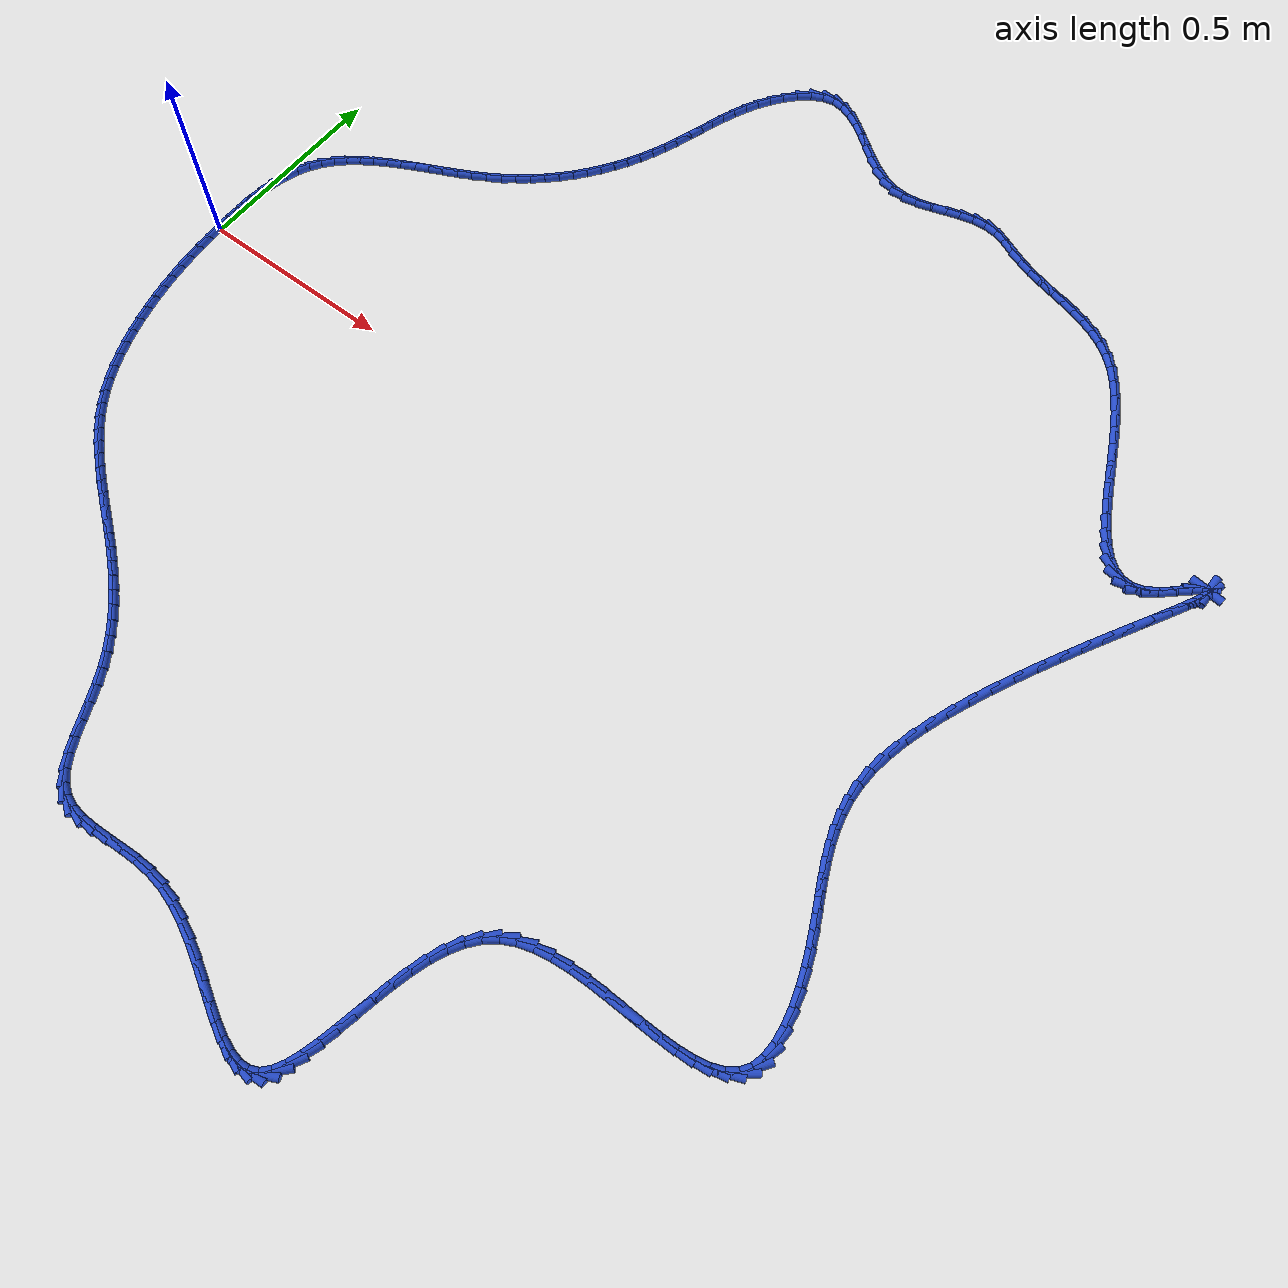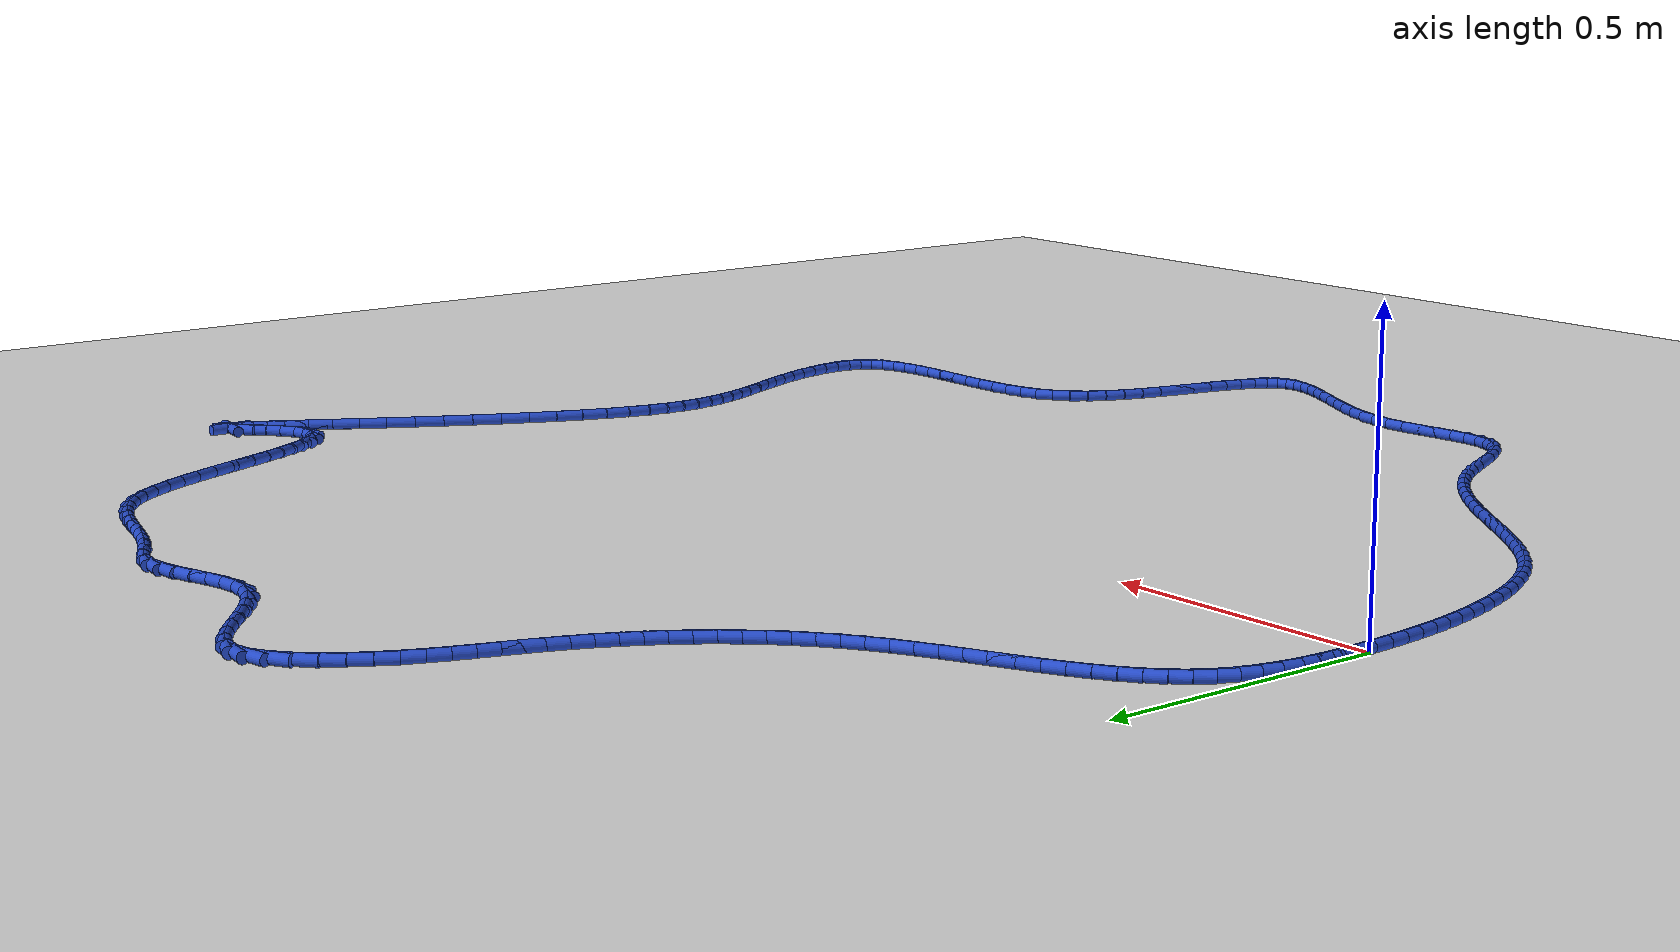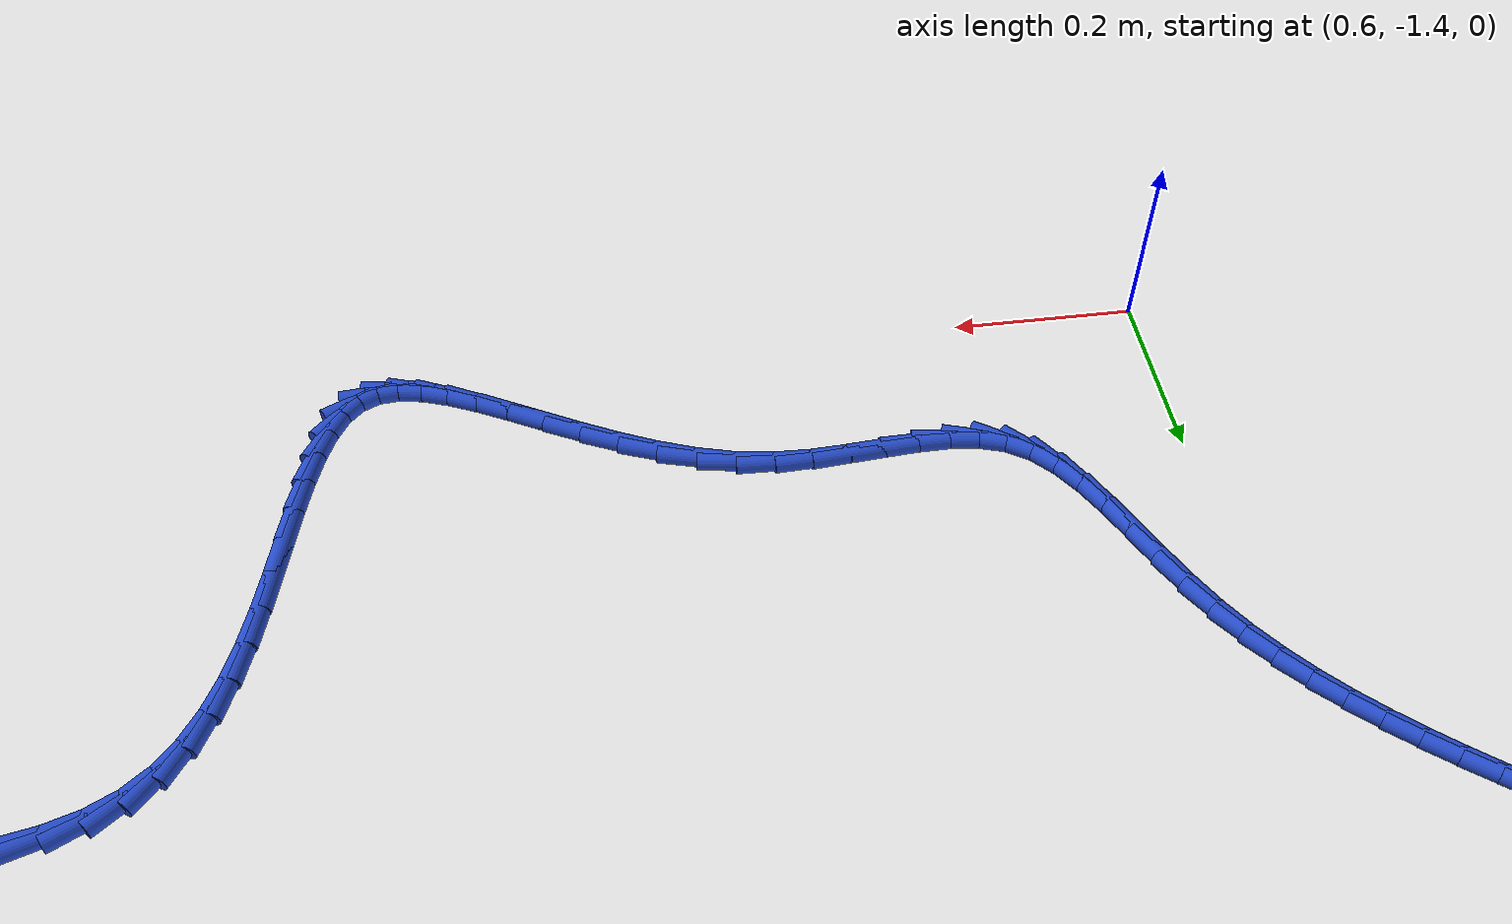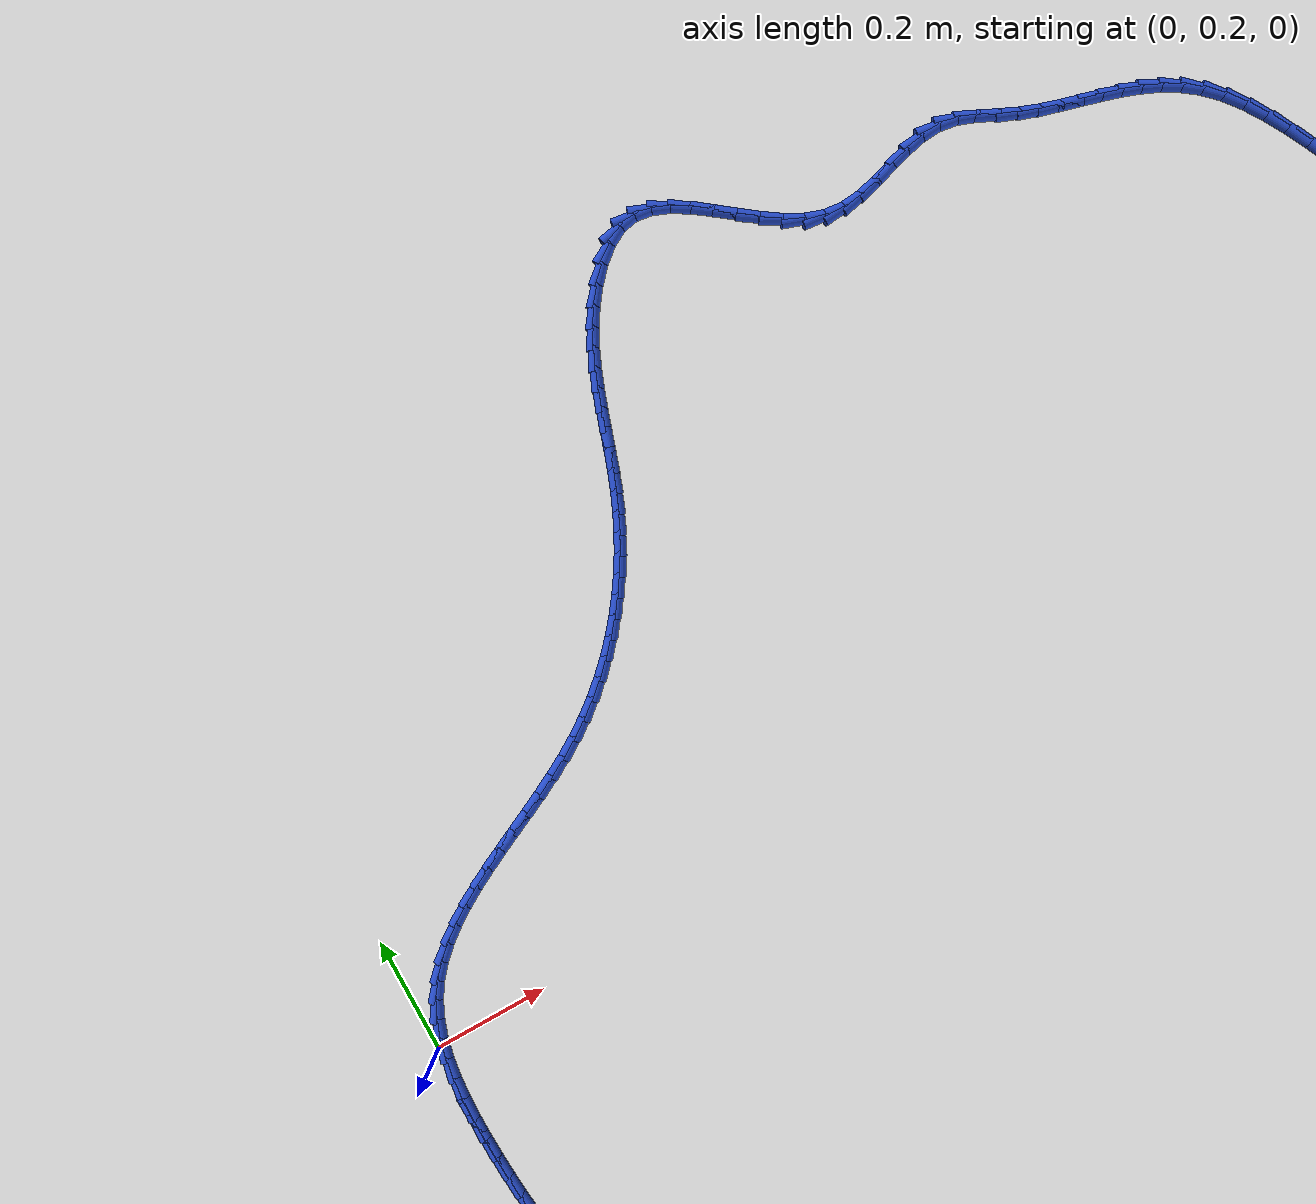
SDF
<sdf version="1.6">
 <world name="default">
  <light name="sun" type="directional">
   <pose>0 0 10 0 -0 0</pose>
   <diffuse>0.8 0.8 0.8 1</diffuse>
   <specular>0.2 0.2 0.2 1</specular>
   <attenuation>
    <range>1000</range>
    <constant>0.9</constant>
    <linear>0.01</linear>
    <quadratic>0.001</quadratic>
   </attenuation>
   <direction>-0.5 0.1 -0.9</direction>
  </light>
  <model name="ground_plane">
   <static>1</static>
   <link name="link">
    <collision name="collision">
     <geometry><plane><normal>0 0 1</normal><size>100 100</size></plane></geometry>
     <surface><friction><ode><mu>100</mu><mu2>50</mu2></ode></friction></surface>
    </collision>
    <visual name="visual">
     <cast_shadows>0</cast_shadows>
     <geometry><plane><normal>0 0 1</normal><size>100 100</size></plane></geometry>
     <material>
      <script><uri>file://media/materials/scripts/gazebo.material</uri><name>Gazebo/WhiteGlow</name></script>
     </material>
    </visual>
   </link>
  </model>
  <gravity>0 0 -9.8</gravity>
  <magnetic_field>6e-06 2.3e-05 -4.2e-05</magnetic_field>
  <atmosphere type="adiabatic"/>
  <physics name="default_physics" default="0" type="ode">
   <max_step_size>0.001</max_step_size>
   <real_time_factor>1</real_time_factor>
   <real_time_update_rate>1000</real_time_update_rate>
  </physics>
  <scene><ambient>0.4 0.4 0.4 1</ambient><background>0.7 0.7 0.7 1</background><shadows>1</shadows></scene>
  <spherical_coordinates>
   <surface_model>EARTH_WGS84</surface_model>
   <latitude_deg>0</latitude_deg>
   <longitude_deg>0</longitude_deg>
   <elevation>0</elevation>
   <heading_deg>0</heading_deg>
  </spherical_coordinates>
  <model name="line">
   <link name="link_0">
    <pose>2.6386770372865964e-17 -6.245004513516506e-17 0.01 0 1.57 -1.5356055546608178</pose>
    <collision name="collision">
     <geometry><cylinder><radius>0.01</radius><length>0.08</length></cylinder></geometry>
    </collision>
    <visual name="visual">
     <material>
      <script><name>Gazebo/Blue</name><uri>file://media/materials/scripts/gazebo.material</uri></script>
     </material>
     <geometry><cylinder><radius>0.01</radius><length>0.08</length></cylinder></geometry>
    </visual>
   </link>
   <link name="link_1">
    <pose>-0.0012859215113197296 0.03652635521292729 0.01 0 1.57 -1.5630723326026337</pose>
    <collision name="collision">
     <geometry><cylinder><radius>0.01</radius><length>0.08</length></cylinder></geometry>
    </collision>
    <visual name="visual">
     <material>
      <script><name>Gazebo/Blue</name><uri>file://media/materials/scripts/gazebo.material</uri></script>
     </material>
     <geometry><cylinder><radius>0.01</radius><length>0.08</length></cylinder></geometry>
    </visual>
   </link>
   <link name="link_2">
    <pose>-0.0015701296713868072 0.0733211146352177 0.01 0 1.57 1.5403618289181997</pose>
    <collision name="collision">
     <geometry><cylinder><radius>0.01</radius><length>0.08</length></cylinder></geometry>
    </collision>
    <visual name="visual">
     <material>
      <script><name>Gazebo/Blue</name><uri>file://media/materials/scripts/gazebo.material</uri></script>
     </material>
     <geometry><cylinder><radius>0.01</radius><length>0.08</length></cylinder></geometry>
    </visual>
   </link>
   <link name="link_3">
    <pose>-0.00045516800112419204 0.10994460045333272 0.01 0 1.57 1.4901225052156661</pose>
    <collision name="collision">
     <geometry><cylinder><radius>0.01</radius><length>0.08</length></cylinder></geometry>
    </collision>
    <visual name="visual">
     <material>
      <script><name>Gazebo/Blue</name><uri>file://media/materials/scripts/gazebo.material</uri></script>
     </material>
     <geometry><cylinder><radius>0.01</radius><length>0.08</length></cylinder></geometry>
    </visual>
   </link>
   <link name="link_4">
    <pose>0.0024564199785451334 0.14595713485373366 0.01 0 1.57 1.425786116624287</pose>
    <collision name="collision">
     <geometry><cylinder><radius>0.01</radius><length>0.08</length></cylinder></geometry>
    </collision>
    <visual name="visual">
     <material>
      <script><name>Gazebo/Blue</name><uri>file://media/materials/scripts/gazebo.material</uri></script>
     </material>
     <geometry><cylinder><radius>0.01</radius><length>0.08</length></cylinder></geometry>
    </visual>
   </link>
   <link name="link_5">
    <pose>0.007562090746698185 0.180919040022882 0.01 0 1.57 1.3447636216351997</pose>
    <collision name="collision">
     <geometry><cylinder><radius>0.01</radius><length>0.08</length></cylinder></geometry>
    </collision>
    <visual name="visual">
     <material>
      <script><name>Gazebo/Blue</name><uri>file://media/materials/scripts/gazebo.material</uri></script>
     </material>
     <geometry><cylinder><radius>0.01</radius><length>0.08</length></cylinder></geometry>
    </visual>
   </link>
   <link name="link_6">
    <pose>0.015259300782411986 0.21439063814723916 0.01 0 1.57 1.2441365064731917</pose>
    <collision name="collision">
     <geometry><cylinder><radius>0.01</radius><length>0.08</length></cylinder></geometry>
    </collision>
    <visual name="visual">
     <material>
      <script><name>Gazebo/Blue</name><uri>file://media/materials/scripts/gazebo.material</uri></script>
     </material>
     <geometry><cylinder><radius>0.01</radius><length>0.08</length></cylinder></geometry>
    </visual>
   </link>
   <link name="link_7">
    <pose>0.02594550656476354 0.24593225141326658 0.01 0 1.57 1.1213596077069625</pose>
    <collision name="collision">
     <geometry><cylinder><radius>0.01</radius><length>0.08</length></cylinder></geometry>
    </collision>
    <visual name="visual">
     <material>
      <script><name>Gazebo/Blue</name><uri>file://media/materials/scripts/gazebo.material</uri></script>
     </material>
     <geometry><cylinder><radius>0.01</radius><length>0.08</length></cylinder></geometry>
    </visual>
   </link>
   <link name="link_8">
    <pose>0.04001730531521694 0.27510503336460845 0.01 0 1.57 0.9846122050661572</pose>
    <collision name="collision">
     <geometry><cylinder><radius>0.01</radius><length>0.08</length></cylinder></geometry>
    </collision>
    <visual name="visual">
     <material>
      <script><name>Gazebo/Blue</name><uri>file://media/materials/scripts/gazebo.material</uri></script>
     </material>
     <geometry><cylinder><radius>0.01</radius><length>0.08</length></cylinder></geometry>
    </visual>
   </link>
   <link name="link_9">
    <pose>0.057660380358999806 0.3016742029845734 0.01 0 1.57 0.8581073378328359</pose>
    <collision name="collision">
     <geometry><cylinder><radius>0.01</radius><length>0.08</length></cylinder></geometry>
    </collision>
    <visual name="visual">
     <material>
      <script><name>Gazebo/Blue</name><uri>file://media/materials/scripts/gazebo.material</uri></script>
     </material>
     <geometry><cylinder><radius>0.01</radius><length>0.08</length></cylinder></geometry>
    </visual>
   </link>
   <link name="link_10">
    <pose>0.07857486763970867 0.3258747607250155 0.01 0 1.57 0.7487419715797645</pose>
    <collision name="collision">
     <geometry><cylinder><radius>0.01</radius><length>0.08</length></cylinder></geometry>
    </collision>
    <visual name="visual">
     <material>
      <script><name>Gazebo/Blue</name><uri>file://media/materials/scripts/gazebo.material</uri></script>
     </material>
     <geometry><cylinder><radius>0.01</radius><length>0.08</length></cylinder></geometry>
    </visual>
   </link>
   <link name="link_11">
    <pose>0.10239282074968625 0.34800757872851135 0.01 0 1.57 0.6579338277247764</pose>
    <collision name="collision">
     <geometry><cylinder><radius>0.01</radius><length>0.08</length></cylinder></geometry>
    </collision>
    <visual name="visual">
     <material>
      <script><name>Gazebo/Blue</name><uri>file://media/materials/scripts/gazebo.material</uri></script>
     </material>
     <geometry><cylinder><radius>0.01</radius><length>0.08</length></cylinder></geometry>
    </visual>
   </link>
   <link name="link_12">
    <pose>0.12874629328127532 0.3683735291376379 0.01 0 1.57 0.5852284718221454</pose>
    <collision name="collision">
     <geometry><cylinder><radius>0.01</radius><length>0.08</length></cylinder></geometry>
    </collision>
    <visual name="visual">
     <material>
      <script><name>Gazebo/Blue</name><uri>file://media/materials/scripts/gazebo.material</uri></script>
     </material>
     <geometry><cylinder><radius>0.01</radius><length>0.08</length></cylinder></geometry>
    </visual>
   </link>
   <link name="link_13">
    <pose>0.1572673388268185 0.38727348409497153 0.01 0 1.57 0.5292492106829894</pose>
    <collision name="collision">
     <geometry><cylinder><radius>0.01</radius><length>0.08</length></cylinder></geometry>
    </collision>
    <visual name="visual">
     <material>
      <script><name>Gazebo/Blue</name><uri>file://media/materials/scripts/gazebo.material</uri></script>
     </material>
     <geometry><cylinder><radius>0.01</radius><length>0.08</length></cylinder></geometry>
    </visual>
   </link>
   <link name="link_14">
    <pose>0.18758801097865865 0.4050083157430891 0.01 0 1.57 0.4883865926694028</pose>
    <collision name="collision">
     <geometry><cylinder><radius>0.01</radius><length>0.08</length></cylinder></geometry>
    </collision>
    <visual name="visual">
     <material>
      <script><name>Gazebo/Blue</name><uri>file://media/materials/scripts/gazebo.material</uri></script>
     </material>
     <geometry><cylinder><radius>0.01</radius><length>0.08</length></cylinder></geometry>
    </visual>
   </link>
   <link name="link_15">
    <pose>0.21934036332913837 0.42187889622456726 0.01 0 1.57 0.4611862426254339</pose>
    <collision name="collision">
     <geometry><cylinder><radius>0.01</radius><length>0.08</length></cylinder></geometry>
    </collision>
    <visual name="visual">
     <material>
      <script><name>Gazebo/Blue</name><uri>file://media/materials/scripts/gazebo.material</uri></script>
     </material>
     <geometry><cylinder><radius>0.01</radius><length>0.08</length></cylinder></geometry>
    </visual>
   </link>
   <link name="link_16">
    <pose>0.2521564494706003 0.43818609768198263 0.01 0 1.57 0.44652503722079323</pose>
    <collision name="collision">
     <geometry><cylinder><radius>0.01</radius><length>0.08</length></cylinder></geometry>
    </collision>
    <visual name="visual">
     <material>
      <script><name>Gazebo/Blue</name><uri>file://media/materials/scripts/gazebo.material</uri></script>
     </material>
     <geometry><cylinder><radius>0.01</radius><length>0.08</length></cylinder></geometry>
    </visual>
   </link>
   <link name="link_17">
    <pose>0.2856683229953873 0.45423079225791196 0.01 0 1.57 0.4436700247904026</pose>
    <collision name="collision">
     <geometry><cylinder><radius>0.01</radius><length>0.08</length></cylinder></geometry>
    </collision>
    <visual name="visual">
     <material>
      <script><name>Gazebo/Blue</name><uri>file://media/materials/scripts/gazebo.material</uri></script>
     </material>
     <geometry><cylinder><radius>0.01</radius><length>0.08</length></cylinder></geometry>
    </visual>
   </link>
   <link name="link_18">
    <pose>0.31950803749584206 0.470313852094932 0.01 0 1.57 0.45228178848544115</pose>
    <collision name="collision">
     <geometry><cylinder><radius>0.01</radius><length>0.08</length></cylinder></geometry>
    </collision>
    <visual name="visual">
     <material>
      <script><name>Gazebo/Blue</name><uri>file://media/materials/scripts/gazebo.material</uri></script>
     </material>
     <geometry><cylinder><radius>0.01</radius><length>0.08</length></cylinder></geometry>
    </visual>
   </link>
   <link name="link_19">
    <pose>0.3533076465643073 0.4867361493356194 0.01 0 1.57 0.472392711204192</pose>
    <collision name="collision">
     <geometry><cylinder><radius>0.01</radius><length>0.08</length></cylinder></geometry>
    </collision>
    <visual name="visual">
     <material>
      <script><name>Gazebo/Blue</name><uri>file://media/materials/scripts/gazebo.material</uri></script>
     </material>
     <geometry><cylinder><radius>0.01</radius><length>0.08</length></cylinder></geometry>
    </visual>
   </link>
   <link name="link_20">
    <pose>0.3866992037931257 0.5037985561225509 0.01 0 1.57 0.5043680207974137</pose>
    <collision name="collision">
     <geometry><cylinder><radius>0.01</radius><length>0.08</length></cylinder></geometry>
    </collision>
    <visual name="visual">
     <material>
      <script><name>Gazebo/Blue</name><uri>file://media/materials/scripts/gazebo.material</uri></script>
     </material>
     <geometry><cylinder><radius>0.01</radius><length>0.08</length></cylinder></geometry>
    </visual>
   </link>
   <link name="link_21">
    <pose>0.4193147627746399 0.521801944598303 0.01 0 1.57 0.5488405969562765</pose>
    <collision name="collision">
     <geometry><cylinder><radius>0.01</radius><length>0.08</length></cylinder></geometry>
    </collision>
    <visual name="visual">
     <material>
      <script><name>Gazebo/Blue</name><uri>file://media/materials/scripts/gazebo.material</uri></script>
     </material>
     <geometry><cylinder><radius>0.01</radius><length>0.08</length></cylinder></geometry>
    </visual>
   </link>
   <link name="link_22">
    <pose>0.450786377109044 0.5410471868973654 0.01 0 1.57 0.6041317047802777</pose>
    <collision name="collision">
     <geometry><cylinder><radius>0.01</radius><length>0.08</length></cylinder></geometry>
    </collision>
    <visual name="visual">
     <material>
      <script><name>Gazebo/Blue</name><uri>file://media/materials/scripts/gazebo.material</uri></script>
     </material>
     <geometry><cylinder><radius>0.01</radius><length>0.08</length></cylinder></geometry>
    </visual>
   </link>
   <link name="link_23">
    <pose>0.48080956747367437 0.5617697800733801 0.01 0 1.57 0.6609411289230461</pose>
    <collision name="collision">
     <geometry><cylinder><radius>0.01</radius><length>0.08</length></cylinder></geometry>
    </collision>
    <visual name="visual">
     <material>
      <script><name>Gazebo/Blue</name><uri>file://media/materials/scripts/gazebo.material</uri></script>
     </material>
     <geometry><cylinder><radius>0.01</radius><length>0.08</length></cylinder></geometry>
    </visual>
   </link>
   <link name="link_24">
    <pose>0.5093299376455233 0.58394761985983 0.01 0 1.57 0.7167491741804481</pose>
    <collision name="collision">
     <geometry><cylinder><radius>0.01</radius><length>0.08</length></cylinder></geometry>
    </collision>
    <visual name="visual">
     <material>
      <script><name>Gazebo/Blue</name><uri>file://media/materials/scripts/gazebo.material</uri></script>
     </material>
     <geometry><cylinder><radius>0.01</radius><length>0.08</length></cylinder></geometry>
    </visual>
   </link>
   <link name="link_25">
    <pose>0.5363546799417076 0.6074951619206179 0.01 0 1.57 0.7714099032592656</pose>
    <collision name="collision">
     <geometry><cylinder><radius>0.01</radius><length>0.08</length></cylinder></geometry>
    </collision>
    <visual name="visual">
     <material>
      <script><name>Gazebo/Blue</name><uri>file://media/materials/scripts/gazebo.material</uri></script>
     </material>
     <geometry><cylinder><radius>0.01</radius><length>0.08</length></cylinder></geometry>
    </visual>
   </link>
   <link name="link_26">
    <pose>0.5618909866793449 0.6323268619196474 0.01 0 1.57 0.824815396915963</pose>
    <collision name="collision">
     <geometry><cylinder><radius>0.01</radius><length>0.08</length></cylinder></geometry>
    </collision>
    <visual name="visual">
     <material>
      <script><name>Gazebo/Blue</name><uri>file://media/materials/scripts/gazebo.material</uri></script>
     </material>
     <geometry><cylinder><radius>0.01</radius><length>0.08</length></cylinder></geometry>
    </visual>
   </link>
   <link name="link_27">
    <pose>0.5859460501755525 0.6583571755208212 0.01 0 1.57 0.8768951348888644</pose>
    <collision name="collision">
     <geometry><cylinder><radius>0.01</radius><length>0.08</length></cylinder></geometry>
    </collision>
    <visual name="visual">
     <material>
      <script><name>Gazebo/Blue</name><uri>file://media/materials/scripts/gazebo.material</uri></script>
     </material>
     <geometry><cylinder><radius>0.01</radius><length>0.08</length></cylinder></geometry>
    </visual>
   </link>
   <link name="link_28">
    <pose>0.6085270627474474 0.6855005583880425 0.01 0 1.57 0.9276139635343557</pose>
    <collision name="collision">
     <geometry><cylinder><radius>0.01</radius><length>0.08</length></cylinder></geometry>
    </collision>
    <visual name="visual">
     <material>
      <script><name>Gazebo/Blue</name><uri>file://media/materials/scripts/gazebo.material</uri></script>
     </material>
     <geometry><cylinder><radius>0.01</radius><length>0.08</length></cylinder></geometry>
    </visual>
   </link>
   <link name="link_29">
    <pose>0.629641216712147 0.7136714661852142 0.01 0 1.57 0.9769690754577881</pose>
    <collision name="collision">
     <geometry><cylinder><radius>0.01</radius><length>0.08</length></cylinder></geometry>
    </collision>
    <visual name="visual">
     <material>
      <script><name>Gazebo/Blue</name><uri>file://media/materials/scripts/gazebo.material</uri></script>
     </material>
     <geometry><cylinder><radius>0.01</radius><length>0.08</length></cylinder></geometry>
    </visual>
   </link>
   <link name="link_30">
    <pose>0.6492957043867685 0.7427843545762395 0.01 0 1.57 1.024986415540435</pose>
    <collision name="collision">
     <geometry><cylinder><radius>0.01</radius><length>0.08</length></cylinder></geometry>
    </collision>
    <visual name="visual">
     <material>
      <script><name>Gazebo/Blue</name><uri>file://media/materials/scripts/gazebo.material</uri></script>
     </material>
     <geometry><cylinder><radius>0.01</radius><length>0.08</length></cylinder></geometry>
    </visual>
   </link>
   <link name="link_31">
    <pose>0.6674977180884293 0.7727536792250214 0.01 0 1.57 1.0717168755039255</pose>
    <collision name="collision">
     <geometry><cylinder><radius>0.01</radius><length>0.08</length></cylinder></geometry>
    </collision>
    <visual name="visual">
     <material>
      <script><name>Gazebo/Blue</name><uri>file://media/materials/scripts/gazebo.material</uri></script>
     </material>
     <geometry><cylinder><radius>0.01</radius><length>0.08</length></cylinder></geometry>
    </visual>
   </link>
   <link name="link_32">
    <pose>0.6842544501342464 0.8034938957954632 0.01 0 1.57 1.1172325649504393</pose>
    <collision name="collision">
     <geometry><cylinder><radius>0.01</radius><length>0.08</length></cylinder></geometry>
    </collision>
    <visual name="visual">
     <material>
      <script><name>Gazebo/Blue</name><uri>file://media/materials/scripts/gazebo.material</uri></script>
     </material>
     <geometry><cylinder><radius>0.01</radius><length>0.08</length></cylinder></geometry>
    </visual>
   </link>
   <link name="link_33">
    <pose>0.6995730928413372 0.8349194599514675 0.01 0 1.57 1.1616233670008453</pose>
    <collision name="collision">
     <geometry><cylinder><radius>0.01</radius><length>0.08</length></cylinder></geometry>
    </collision>
    <visual name="visual">
     <material>
      <script><name>Gazebo/Blue</name><uri>file://media/materials/scripts/gazebo.material</uri></script>
     </material>
     <geometry><cylinder><radius>0.01</radius><length>0.08</length></cylinder></geometry>
    </visual>
   </link>
   <link name="link_34">
    <pose>0.7134608385268189 0.866944827356938 0.01 0 1.57 1.2034568578909017</pose>
    <collision name="collision">
     <geometry><cylinder><radius>0.01</radius><length>0.08</length></cylinder></geometry>
    </collision>
    <visual name="visual">
     <material>
      <script><name>Gazebo/Blue</name><uri>file://media/materials/scripts/gazebo.material</uri></script>
     </material>
     <geometry><cylinder><radius>0.01</radius><length>0.08</length></cylinder></geometry>
    </visual>
   </link>
   <link name="link_35">
    <pose>0.7259781852926838 0.8994738469741528 0.01 0 1.57 1.233446599249353</pose>
    <collision name="collision">
     <geometry><cylinder><radius>0.01</radius><length>0.08</length></cylinder></geometry>
    </collision>
    <visual name="visual">
     <material>
      <script><name>Gazebo/Blue</name><uri>file://media/materials/scripts/gazebo.material</uri></script>
     </material>
     <geometry><cylinder><radius>0.01</radius><length>0.08</length></cylinder></geometry>
    </visual>
   </link>
   <link name="link_36">
    <pose>0.7375083986811577 0.9323461440054251 0.01 0 1.57 1.2480430231626474</pose>
    <collision name="collision">
     <geometry><cylinder><radius>0.01</radius><length>0.08</length></cylinder></geometry>
    </collision>
    <visual name="visual">
     <material>
      <script><name>Gazebo/Blue</name><uri>file://media/materials/scripts/gazebo.material</uri></script>
     </material>
     <geometry><cylinder><radius>0.01</radius><length>0.08</length></cylinder></geometry>
    </visual>
   </link>
   <link name="link_37">
    <pose>0.7485555973416003 0.9653772964910049 0.01 0 1.57 1.247229006031626</pose>
    <collision name="collision">
     <geometry><cylinder><radius>0.01</radius><length>0.08</length></cylinder></geometry>
    </collision>
    <visual name="visual">
     <material>
      <script><name>Gazebo/Blue</name><uri>file://media/materials/scripts/gazebo.material</uri></script>
     </material>
     <geometry><cylinder><radius>0.01</radius><length>0.08</length></cylinder></geometry>
    </visual>
   </link>
   <link name="link_38">
    <pose>0.7596241116926526 0.998382840333622 0.01 0 1.57 1.2309808173151962</pose>
    <collision name="collision">
     <geometry><cylinder><radius>0.01</radius><length>0.08</length></cylinder></geometry>
    </collision>
    <visual name="visual">
     <material>
      <script><name>Gazebo/Blue</name><uri>file://media/materials/scripts/gazebo.material</uri></script>
     </material>
     <geometry><cylinder><radius>0.01</radius><length>0.08</length></cylinder></geometry>
    </visual>
   </link>
   <link name="link_39">
    <pose>0.7712182721529552 1.0311783114360074 0.01 0 1.57 1.1992678507592647</pose>
    <collision name="collision">
     <geometry><cylinder><radius>0.01</radius><length>0.08</length></cylinder></geometry>
    </collision>
    <visual name="visual">
     <material>
      <script><name>Gazebo/Blue</name><uri>file://media/materials/scripts/gazebo.material</uri></script>
     </material>
     <geometry><cylinder><radius>0.01</radius><length>0.08</length></cylinder></geometry>
    </visual>
   </link>
   <link name="link_40">
    <pose>0.7838424091411494 1.0635792457008912 0.01 0 1.57 1.1521689373937378</pose>
    <collision name="collision">
     <geometry><cylinder><radius>0.01</radius><length>0.08</length></cylinder></geometry>
    </collision>
    <visual name="visual">
     <material>
      <script><name>Gazebo/Blue</name><uri>file://media/materials/scripts/gazebo.material</uri></script>
     </material>
     <geometry><cylinder><radius>0.01</radius><length>0.08</length></cylinder></geometry>
    </visual>
   </link>
   <link name="link_41">
    <pose>0.7980008530758755 1.0954011790310036 0.01 0 1.57 1.0900947491056725</pose>
    <collision name="collision">
     <geometry><cylinder><radius>0.01</radius><length>0.08</length></cylinder></geometry>
    </collision>
    <visual name="visual">
     <material>
      <script><name>Gazebo/Blue</name><uri>file://media/materials/scripts/gazebo.material</uri></script>
     </material>
     <geometry><cylinder><radius>0.01</radius><length>0.08</length></cylinder></geometry>
    </visual>
   </link>
   <link name="link_42">
    <pose>0.8141979343757745 1.1264596473290753 0.01 0 1.57 1.014086824967226</pose>
    <collision name="collision">
     <geometry><cylinder><radius>0.01</radius><length>0.08</length></cylinder></geometry>
    </collision>
    <visual name="visual">
     <material>
      <script><name>Gazebo/Blue</name><uri>file://media/materials/scripts/gazebo.material</uri></script>
     </material>
     <geometry><cylinder><radius>0.01</radius><length>0.08</length></cylinder></geometry>
    </visual>
   </link>
   <link name="link_43">
    <pose>0.8329379834594868 1.156570186497836 0.01 0 1.57 0.9261094413567204</pose>
    <collision name="collision">
     <geometry><cylinder><radius>0.01</radius><length>0.08</length></cylinder></geometry>
    </collision>
    <visual name="visual">
     <material>
      <script><name>Gazebo/Blue</name><uri>file://media/materials/scripts/gazebo.material</uri></script>
     </material>
     <geometry><cylinder><radius>0.01</radius><length>0.08</length></cylinder></geometry>
    </visual>
   </link>
   <link name="link_44">
    <pose>0.8547253307456534 1.1855483324400162 0.01 0 1.57 0.8272469703675408</pose>
    <collision name="collision">
     <geometry><cylinder><radius>0.01</radius><length>0.08</length></cylinder></geometry>
    </collision>
    <visual name="visual">
     <material>
      <script><name>Gazebo/Blue</name><uri>file://media/materials/scripts/gazebo.material</uri></script>
     </material>
     <geometry><cylinder><radius>0.01</radius><length>0.08</length></cylinder></geometry>
    </visual>
   </link>
   <link name="link_45">
    <pose>0.8799235861111885 1.2129490792001565 0.01 0 1.57 0.6980427215251891</pose>
    <collision name="collision">
     <geometry><cylinder><radius>0.01</radius><length>0.08</length></cylinder></geometry>
    </collision>
    <visual name="visual">
     <material>
      <script><name>Gazebo/Blue</name><uri>file://media/materials/scripts/gazebo.material</uri></script>
     </material>
     <geometry><cylinder><radius>0.01</radius><length>0.08</length></cylinder></geometry>
    </visual>
   </link>
   <link name="link_46">
    <pose>0.9078379370174183 1.2363677684541832 0.01 0 1.57 0.5012900157537306</pose>
    <collision name="collision">
     <geometry><cylinder><radius>0.01</radius><length>0.08</length></cylinder></geometry>
    </collision>
    <visual name="visual">
     <material>
      <script><name>Gazebo/Blue</name><uri>file://media/materials/scripts/gazebo.material</uri></script>
     </material>
     <geometry><cylinder><radius>0.01</radius><length>0.08</length></cylinder></geometry>
    </visual>
   </link>
   <link name="link_47">
    <pose>0.9372918821117273 1.2525079026545962 0.01 0 1.57 0.1946782709216213</pose>
    <collision name="collision">
     <geometry><cylinder><radius>0.01</radius><length>0.08</length></cylinder></geometry>
    </collision>
    <visual name="visual">
     <material>
      <script><name>Gazebo/Blue</name><uri>file://media/materials/scripts/gazebo.material</uri></script>
     </material>
     <geometry><cylinder><radius>0.01</radius><length>0.08</length></cylinder></geometry>
    </visual>
   </link>
   <link name="link_48">
    <pose>0.9671848943639096 1.2584020737128516 0.01 0 1.57 -0.136798270185684</pose>
    <collision name="collision">
     <geometry><cylinder><radius>0.01</radius><length>0.08</length></cylinder></geometry>
    </collision>
    <visual name="visual">
     <material>
      <script><name>Gazebo/Blue</name><uri>file://media/materials/scripts/gazebo.material</uri></script>
     </material>
     <geometry><cylinder><radius>0.01</radius><length>0.08</length></cylinder></geometry>
    </visual>
   </link>
   <link name="link_49">
    <pose>0.9971666805318862 1.2542748396861931 0.01 0 1.57 -0.38321469248800427</pose>
    <collision name="collision">
     <geometry><cylinder><radius>0.01</radius><length>0.08</length></cylinder></geometry>
    </collision>
    <visual name="visual">
     <material>
      <script><name>Gazebo/Blue</name><uri>file://media/materials/scripts/gazebo.material</uri></script>
     </material>
     <geometry><cylinder><radius>0.01</radius><length>0.08</length></cylinder></geometry>
    </visual>
   </link>
   <link name="link_50">
    <pose>1.0273039925993683 1.2421251311848647 0.01 0 1.57 -0.5388623405360768</pose>
    <collision name="collision">
     <geometry><cylinder><radius>0.01</radius><length>0.08</length></cylinder></geometry>
    </collision>
    <visual name="visual">
     <material>
      <script><name>Gazebo/Blue</name><uri>file://media/materials/scripts/gazebo.material</uri></script>
     </material>
     <geometry><cylinder><radius>0.01</radius><length>0.08</length></cylinder></geometry>
    </visual>
   </link>
   <link name="link_51">
    <pose>1.0576680610684848 1.2239709332517354 0.01 0 1.57 -0.6253968254231684</pose>
    <collision name="collision">
     <geometry><cylinder><radius>0.01</radius><length>0.08</length></cylinder></geometry>
    </collision>
    <visual name="visual">
     <material>
      <script><name>Gazebo/Blue</name><uri>file://media/materials/scripts/gazebo.material</uri></script>
     </material>
     <geometry><cylinder><radius>0.01</radius><length>0.08</length></cylinder></geometry>
    </visual>
   </link>
   <link name="link_52">
    <pose>1.0883301164413632 1.201830230929674 0.01 0 1.57 -0.6605166282434157</pose>
    <collision name="collision">
     <geometry><cylinder><radius>0.01</radius><length>0.08</length></cylinder></geometry>
    </collision>
    <visual name="visual">
     <material>
      <script><name>Gazebo/Blue</name><uri>file://media/materials/scripts/gazebo.material</uri></script>
     </material>
     <geometry><cylinder><radius>0.01</radius><length>0.08</length></cylinder></geometry>
    </visual>
   </link>
   <link name="link_53">
    <pose>1.1193613892201315 1.1777210092615484 0.01 0 1.57 -0.652709195439197</pose>
    <collision name="collision">
     <geometry><cylinder><radius>0.01</radius><length>0.08</length></cylinder></geometry>
    </collision>
    <visual name="visual">
     <material>
      <script><name>Gazebo/Blue</name><uri>file://media/materials/scripts/gazebo.material</uri></script>
     </material>
     <geometry><cylinder><radius>0.01</radius><length>0.08</length></cylinder></geometry>
    </visual>
   </link>
   <link name="link_54">
    <pose>1.1508331099069173 1.1536612532902284 0.01 0 1.57 -0.6023662868372007</pose>
    <collision name="collision">
     <geometry><cylinder><radius>0.01</radius><length>0.08</length></cylinder></geometry>
    </collision>
    <visual name="visual">
     <material>
      <script><name>Gazebo/Blue</name><uri>file://media/materials/scripts/gazebo.material</uri></script>
     </material>
     <geometry><cylinder><radius>0.01</radius><length>0.08</length></cylinder></geometry>
    </visual>
   </link>
   <link name="link_55">
    <pose>1.1828165090038496 1.1316689480585822 0.01 0 1.57 -0.5027347599885018</pose>
    <collision name="collision">
     <geometry><cylinder><radius>0.01</radius><length>0.08</length></cylinder></geometry>
    </collision>
    <visual name="visual">
     <material>
      <script><name>Gazebo/Blue</name><uri>file://media/materials/scripts/gazebo.material</uri></script>
     </material>
     <geometry><cylinder><radius>0.01</radius><length>0.08</length></cylinder></geometry>
    </visual>
   </link>
   <link name="link_56">
    <pose>1.2153828170130563 1.1137620786094786 0.01 0 1.57 -0.34139457595518125</pose>
    <collision name="collision">
     <geometry><cylinder><radius>0.01</radius><length>0.08</length></cylinder></geometry>
    </collision>
    <visual name="visual">
     <material>
      <script><name>Gazebo/Blue</name><uri>file://media/materials/scripts/gazebo.material</uri></script>
     </material>
     <geometry><cylinder><radius>0.01</radius><length>0.08</length></cylinder></geometry>
    </visual>
   </link>
   <link name="link_57">
    <pose>1.2486032644366645 1.101958629985786 0.01 0 1.57 -0.11395972814048469</pose>
    <collision name="collision">
     <geometry><cylinder><radius>0.01</radius><length>0.08</length></cylinder></geometry>
    </collision>
    <visual name="visual">
     <material>
      <script><name>Gazebo/Blue</name><uri>file://media/materials/scripts/gazebo.material</uri></script>
     </material>
     <geometry><cylinder><radius>0.01</radius><length>0.08</length></cylinder></geometry>
    </visual>
   </link>
   <link name="link_58">
    <pose>1.282534931967071 1.0980749596293777 0.01 0 1.57 0.09607817221247528</pose>
    <collision name="collision">
     <geometry><cylinder><radius>0.01</radius><length>0.08</length></cylinder></geometry>
    </collision>
    <visual name="visual">
     <material>
      <script><name>Gazebo/Blue</name><uri>file://media/materials/scripts/gazebo.material</uri></script>
     </material>
     <geometry><cylinder><radius>0.01</radius><length>0.08</length></cylinder></geometry>
    </visual>
   </link>
   <link name="link_59">
    <pose>1.3170576771930904 1.1014020857802107 0.01 0 1.57 0.22847469774608145</pose>
    <collision name="collision">
     <geometry><cylinder><radius>0.01</radius><length>0.08</length></cylinder></geometry>
    </collision>
    <visual name="visual">
     <material>
      <script><name>Gazebo/Blue</name><uri>file://media/materials/scripts/gazebo.material</uri></script>
     </material>
     <geometry><cylinder><radius>0.01</radius><length>0.08</length></cylinder></geometry>
    </visual>
   </link>
   <link name="link_60">
    <pose>1.351930669240402 1.1095112773847458 0.01 0 1.57 0.2897637995066804</pose>
    <collision name="collision">
     <geometry><cylinder><radius>0.01</radius><length>0.08</length></cylinder></geometry>
    </collision>
    <visual name="visual">
     <material>
      <script><name>Gazebo/Blue</name><uri>file://media/materials/scripts/gazebo.material</uri></script>
     </material>
     <geometry><cylinder><radius>0.01</radius><length>0.08</length></cylinder></geometry>
    </visual>
   </link>
   <link name="link_61">
    <pose>1.3869107601669473 1.119940786351168 0.01 0 1.57 0.28710321542571177</pose>
    <collision name="collision">
     <geometry><cylinder><radius>0.01</radius><length>0.08</length></cylinder></geometry>
    </collision>
    <visual name="visual">
     <material>
      <script><name>Gazebo/Blue</name><uri>file://media/materials/scripts/gazebo.material</uri></script>
     </material>
     <geometry><cylinder><radius>0.01</radius><length>0.08</length></cylinder></geometry>
    </visual>
   </link>
   <link name="link_62">
    <pose>1.4217548020306652 1.130228864587663 0.01 0 1.57 0.21938896591605</pose>
    <collision name="collision">
     <geometry><cylinder><radius>0.01</radius><length>0.08</length></cylinder></geometry>
    </collision>
    <visual name="visual">
     <material>
      <script><name>Gazebo/Blue</name><uri>file://media/materials/scripts/gazebo.material</uri></script>
     </material>
     <geometry><cylinder><radius>0.01</radius><length>0.08</length></cylinder></geometry>
    </visual>
   </link>
   <link name="link_63">
    <pose>1.4562196468894981 1.1379137640024177 0.01 0 1.57 0.07726252862373256</pose>
    <collision name="collision">
     <geometry><cylinder><radius>0.01</radius><length>0.08</length></cylinder></geometry>
    </collision>
    <visual name="visual">
     <material>
      <script><name>Gazebo/Blue</name><uri>file://media/materials/scripts/gazebo.material</uri></script>
     </material>
     <geometry><cylinder><radius>0.01</radius><length>0.08</length></cylinder></geometry>
    </visual>
   </link>
   <link name="link_64">
    <pose>1.4900621468013857 1.140533736503617 0.01 0 1.57 -0.14484840193356263</pose>
    <collision name="collision">
     <geometry><cylinder><radius>0.01</radius><length>0.08</length></cylinder></geometry>
    </collision>
    <visual name="visual">
     <material>
      <script><name>Gazebo/Blue</name><uri>file://media/materials/scripts/gazebo.material</uri></script>
     </material>
     <geometry><cylinder><radius>0.01</radius><length>0.08</length></cylinder></geometry>
    </visual>
   </link>
   <link name="link_65">
    <pose>1.5230517323239887 1.1357215456371488 0.01 0 1.57 -0.3514077244487403</pose>
    <collision name="collision">
     <geometry><cylinder><radius>0.01</radius><length>0.08</length></cylinder></geometry>
    </collision>
    <visual name="visual">
     <material>
      <script><name>Gazebo/Blue</name><uri>file://media/materials/scripts/gazebo.material</uri></script>
     </material>
     <geometry><cylinder><radius>0.01</radius><length>0.08</length></cylinder></geometry>
    </visual>
   </link>
   <link name="link_66">
    <pose>1.555327617244323 1.1238884117903467 0.01 0 1.57 -0.4440064988694887</pose>
    <collision name="collision">
     <geometry><cylinder><radius>0.01</radius><length>0.08</length></cylinder></geometry>
    </collision>
    <visual name="visual">
     <material>
      <script><name>Gazebo/Blue</name><uri>file://media/materials/scripts/gazebo.material</uri></script>
     </material>
     <geometry><cylinder><radius>0.01</radius><length>0.08</length></cylinder></geometry>
    </visual>
   </link>
   <link name="link_67">
    <pose>1.5874499465156224 1.1086083247400593 0.01 0 1.57 -0.43175485344814746</pose>
    <collision name="collision">
     <geometry><cylinder><radius>0.01</radius><length>0.08</length></cylinder></geometry>
    </collision>
    <visual name="visual">
     <material>
      <script><name>Gazebo/Blue</name><uri>file://media/materials/scripts/gazebo.material</uri></script>
     </material>
     <geometry><cylinder><radius>0.01</radius><length>0.08</length></cylinder></geometry>
    </visual>
   </link>
   <link name="link_68">
    <pose>1.6199987642933193 1.0936115645586553 0.01 0 1.57 -0.3595593047896718</pose>
    <collision name="collision">
     <geometry><cylinder><radius>0.01</radius><length>0.08</length></cylinder></geometry>
    </collision>
    <visual name="visual">
     <material>
      <script><name>Gazebo/Blue</name><uri>file://media/materials/scripts/gazebo.material</uri></script>
     </material>
     <geometry><cylinder><radius>0.01</radius><length>0.08</length></cylinder></geometry>
    </visual>
   </link>
   <link name="link_69">
    <pose>1.6532631805868956 1.0811074770422702 0.01 0 1.57 -0.3039631590371445</pose>
    <collision name="collision">
     <geometry><cylinder><radius>0.01</radius><length>0.08</length></cylinder></geometry>
    </collision>
    <visual name="visual">
     <material>
      <script><name>Gazebo/Blue</name><uri>file://media/materials/scripts/gazebo.material</uri></script>
     </material>
     <geometry><cylinder><radius>0.01</radius><length>0.08</length></cylinder></geometry>
    </visual>
   </link>
   <link name="link_70">
    <pose>1.6870003851848916 1.070524656028142 0.01 0 1.57 -0.2739551416541571</pose>
    <collision name="collision">
     <geometry><cylinder><radius>0.01</radius><length>0.08</length></cylinder></geometry>
    </collision>
    <visual name="visual">
     <material>
      <script><name>Gazebo/Blue</name><uri>file://media/materials/scripts/gazebo.material</uri></script>
     </material>
     <geometry><cylinder><radius>0.01</radius><length>0.08</length></cylinder></geometry>
    </visual>
   </link>
   <link name="link_71">
    <pose>1.7209108352063052 1.0609951104978321 0.01 0 1.57 -0.26984113333690357</pose>
    <collision name="collision">
     <geometry><cylinder><radius>0.01</radius><length>0.08</length></cylinder></geometry>
    </collision>
    <visual name="visual">
     <material>
      <script><name>Gazebo/Blue</name><uri>file://media/materials/scripts/gazebo.material</uri></script>
     </material>
     <geometry><cylinder><radius>0.01</radius><length>0.08</length></cylinder></geometry>
    </visual>
   </link>
   <link name="link_72">
    <pose>1.7546949877701359 1.0516508494329015 0.01 0 1.57 -0.2919922873287161</pose>
    <collision name="collision">
     <geometry><cylinder><radius>0.01</radius><length>0.08</length></cylinder></geometry>
    </collision>
    <visual name="visual">
     <material>
      <script><name>Gazebo/Blue</name><uri>file://media/materials/scripts/gazebo.material</uri></script>
     </material>
     <geometry><cylinder><radius>0.01</radius><length>0.08</length></cylinder></geometry>
    </visual>
   </link>
   <link name="link_73">
    <pose>1.7880532999953818 1.0416238818149108 0.01 0 1.57 -0.3409310172532891</pose>
    <collision name="collision">
     <geometry><cylinder><radius>0.01</radius><length>0.08</length></cylinder></geometry>
    </collision>
    <visual name="visual">
     <material>
      <script><name>Gazebo/Blue</name><uri>file://media/materials/scripts/gazebo.material</uri></script>
     </material>
     <geometry><cylinder><radius>0.01</radius><length>0.08</length></cylinder></geometry>
    </visual>
   </link>
   <link name="link_74">
    <pose>1.8206862290010413 1.0300462166254205 0.01 0 1.57 -0.41685902731152863</pose>
    <collision name="collision">
     <geometry><cylinder><radius>0.01</radius><length>0.08</length></cylinder></geometry>
    </collision>
    <visual name="visual">
     <material>
      <script><name>Gazebo/Blue</name><uri>file://media/materials/scripts/gazebo.material</uri></script>
     </material>
     <geometry><cylinder><radius>0.01</radius><length>0.08</length></cylinder></geometry>
    </visual>
   </link>
   <link name="link_75">
    <pose>1.8522942319061138 1.016049862845992 0.01 0 1.57 -0.5186022053603065</pose>
    <collision name="collision">
     <geometry><cylinder><radius>0.01</radius><length>0.08</length></cylinder></geometry>
    </collision>
    <visual name="visual">
     <material>
      <script><name>Gazebo/Blue</name><uri>file://media/materials/scripts/gazebo.material</uri></script>
     </material>
     <geometry><cylinder><radius>0.01</radius><length>0.08</length></cylinder></geometry>
    </visual>
   </link>
   <link name="link_76">
    <pose>1.8825777658295972 0.9987668294581855 0.01 0 1.57 -0.6422284154508868</pose>
    <collision name="collision">
     <geometry><cylinder><radius>0.01</radius><length>0.08</length></cylinder></geometry>
    </collision>
    <visual name="visual">
     <material>
      <script><name>Gazebo/Blue</name><uri>file://media/materials/scripts/gazebo.material</uri></script>
     </material>
     <geometry><cylinder><radius>0.01</radius><length>0.08</length></cylinder></geometry>
    </visual>
   </link>
   <link name="link_77">
    <pose>1.9112372878904909 0.9773291254435618 0.01 0 1.57 -0.7796934066819615</pose>
    <collision name="collision">
     <geometry><cylinder><radius>0.01</radius><length>0.08</length></cylinder></geometry>
    </collision>
    <visual name="visual">
     <material>
      <script><name>Gazebo/Blue</name><uri>file://media/materials/scripts/gazebo.material</uri></script>
     </material>
     <geometry><cylinder><radius>0.01</radius><length>0.08</length></cylinder></geometry>
    </visual>
   </link>
   <link name="link_78">
    <pose>1.9379797325084764 0.9508900716271254 0.01 0 1.57 -0.9047093194507138</pose>
    <collision name="collision">
     <geometry><cylinder><radius>0.01</radius><length>0.08</length></cylinder></geometry>
    </collision>
    <visual name="visual">
     <material>
      <script><name>Gazebo/Blue</name><uri>file://media/materials/scripts/gazebo.material</uri></script>
     </material>
     <geometry><cylinder><radius>0.01</radius><length>0.08</length></cylinder></geometry>
    </visual>
   </link>
   <link name="link_79">
    <pose>1.9627469240330444 0.9193758319755952 0.01 0 1.57 -0.9977627869747383</pose>
    <collision name="collision">
     <geometry><cylinder><radius>0.01</radius><length>0.08</length></cylinder></geometry>
    </collision>
    <visual name="visual">
     <material>
      <script><name>Gazebo/Blue</name><uri>file://media/materials/scripts/gazebo.material</uri></script>
     </material>
     <geometry><cylinder><radius>0.01</radius><length>0.08</length></cylinder></geometry>
    </visual>
   </link>
   <link name="link_80">
    <pose>1.98577637692691 0.8836854605079247 0.01 0 1.57 -1.0649965970787165</pose>
    <collision name="collision">
     <geometry><cylinder><radius>0.01</radius><length>0.08</length></cylinder></geometry>
    </collision>
    <visual name="visual">
     <material>
      <script><name>Gazebo/Blue</name><uri>file://media/materials/scripts/gazebo.material</uri></script>
     </material>
     <geometry><cylinder><radius>0.01</radius><length>0.08</length></cylinder></geometry>
    </visual>
   </link>
   <link name="link_81">
    <pose>2.0073244453384715 0.8447799982421857 0.01 0 1.57 -1.1121508738034331</pose>
    <collision name="collision">
     <geometry><cylinder><radius>0.01</radius><length>0.08</length></cylinder></geometry>
    </collision>
    <visual name="visual">
     <material>
      <script><name>Gazebo/Blue</name><uri>file://media/materials/scripts/gazebo.material</uri></script>
     </material>
     <geometry><cylinder><radius>0.01</radius><length>0.08</length></cylinder></geometry>
    </visual>
   </link>
   <link name="link_82">
    <pose>2.0276474834161275 0.8036204861964529 0.01 0 1.57 -1.1430417790752947</pose>
    <collision name="collision">
     <geometry><cylinder><radius>0.01</radius><length>0.08</length></cylinder></geometry>
    </collision>
    <visual name="visual">
     <material>
      <script><name>Gazebo/Blue</name><uri>file://media/materials/scripts/gazebo.material</uri></script>
     </material>
     <geometry><cylinder><radius>0.01</radius><length>0.08</length></cylinder></geometry>
    </visual>
   </link>
   <link name="link_83">
    <pose>2.0470018453082766 0.7611679653887987 0.01 0 1.57 -1.1598812377643082</pose>
    <collision name="collision">
     <geometry><cylinder><radius>0.01</radius><length>0.08</length></cylinder></geometry>
    </collision>
    <visual name="visual">
     <material>
      <script><name>Gazebo/Blue</name><uri>file://media/materials/scripts/gazebo.material</uri></script>
     </material>
     <geometry><cylinder><radius>0.01</radius><length>0.08</length></cylinder></geometry>
    </visual>
   </link>
   <link name="link_84">
    <pose>2.065643885163317 0.7183834768372979 0.01 0 1.57 -1.163512818470548</pose>
    <collision name="collision">
     <geometry><cylinder><radius>0.01</radius><length>0.08</length></cylinder></geometry>
    </collision>
    <visual name="visual">
     <material>
      <script><name>Gazebo/Blue</name><uri>file://media/materials/scripts/gazebo.material</uri></script>
     </material>
     <geometry><cylinder><radius>0.01</radius><length>0.08</length></cylinder></geometry>
    </visual>
   </link>
   <link name="link_85">
    <pose>2.083829957129649 0.6762280615600227 0.01 0 1.57 -1.1534485427687924</pose>
    <collision name="collision">
     <geometry><cylinder><radius>0.01</radius><length>0.08</length></cylinder></geometry>
    </collision>
    <visual name="visual">
     <material>
      <script><name>Gazebo/Blue</name><uri>file://media/materials/scripts/gazebo.material</uri></script>
     </material>
     <geometry><cylinder><radius>0.01</radius><length>0.08</length></cylinder></geometry>
    </visual>
   </link>
   <link name="link_86">
    <pose>2.1018164153556698 0.6356627605750473 0.01 0 1.57 -1.127638226678052</pose>
    <collision name="collision">
     <geometry><cylinder><radius>0.01</radius><length>0.08</length></cylinder></geometry>
    </collision>
    <visual name="visual">
     <material>
      <script><name>Gazebo/Blue</name><uri>file://media/materials/scripts/gazebo.material</uri></script>
     </material>
     <geometry><cylinder><radius>0.01</radius><length>0.08</length></cylinder></geometry>
    </visual>
   </link>
   <link name="link_87">
    <pose>2.1198596139897776 0.597648614900445 0.01 0 1.57 -1.081849261386643</pose>
    <collision name="collision">
     <geometry><cylinder><radius>0.01</radius><length>0.08</length></cylinder></geometry>
    </collision>
    <visual name="visual">
     <material>
      <script><name>Gazebo/Blue</name><uri>file://media/materials/scripts/gazebo.material</uri></script>
     </material>
     <geometry><cylinder><radius>0.01</radius><length>0.08</length></cylinder></geometry>
    </visual>
   </link>
   <link name="link_88">
    <pose>2.1382159071803724 0.5631466655542886 0.01 0 1.57 -1.008427151818762</pose>
    <collision name="collision">
     <geometry><cylinder><radius>0.01</radius><length>0.08</length></cylinder></geometry>
    </collision>
    <visual name="visual">
     <material>
      <script><name>Gazebo/Blue</name><uri>file://media/materials/scripts/gazebo.material</uri></script>
     </material>
     <geometry><cylinder><radius>0.01</radius><length>0.08</length></cylinder></geometry>
    </visual>
   </link>
   <link name="link_89">
    <pose>2.157141649075852 0.5331179535546526 0.01 0 1.57 -0.8941740504548429</pose>
    <collision name="collision">
     <geometry><cylinder><radius>0.01</radius><length>0.08</length></cylinder></geometry>
    </collision>
    <visual name="visual">
     <material>
      <script><name>Gazebo/Blue</name><uri>file://media/materials/scripts/gazebo.material</uri></script>
     </material>
     <geometry><cylinder><radius>0.01</radius><length>0.08</length></cylinder></geometry>
    </visual>
   </link>
   <link name="link_90">
    <pose>2.1768931938246143 0.5085235199196095 0.01 0 1.57 -0.7180036534411387</pose>
    <collision name="collision">
     <geometry><cylinder><radius>0.01</radius><length>0.08</length></cylinder></geometry>
    </collision>
    <visual name="visual">
     <material>
      <script><name>Gazebo/Blue</name><uri>file://media/materials/scripts/gazebo.material</uri></script>
     </material>
     <geometry><cylinder><radius>0.01</radius><length>0.08</length></cylinder></geometry>
    </visual>
   </link>
   <link name="link_91">
    <pose>2.1977268955750584 0.49032440566723345 0.01 0 1.57 -0.4548286662205804</pose>
    <collision name="collision">
     <geometry><cylinder><radius>0.01</radius><length>0.08</length></cylinder></geometry>
    </collision>
    <visual name="visual">
     <material>
      <script><name>Gazebo/Blue</name><uri>file://media/materials/scripts/gazebo.material</uri></script>
     </material>
     <geometry><cylinder><radius>0.01</radius><length>0.08</length></cylinder></geometry>
    </visual>
   </link>
   <link name="link_92">
    <pose>2.2198991084755844 0.4794816518155976 0.01 0 1.57 -0.10585704164938609</pose>
    <collision name="collision">
     <geometry><cylinder><radius>0.01</radius><length>0.08</length></cylinder></geometry>
    </collision>
    <visual name="visual">
     <material>
      <script><name>Gazebo/Blue</name><uri>file://media/materials/scripts/gazebo.material</uri></script>
     </material>
     <geometry><cylinder><radius>0.01</radius><length>0.08</length></cylinder></geometry>
    </visual>
   </link>
   <link name="link_93">
    <pose>2.2436661866745884 0.4769562993827754 0.01 0 1.57 0.2577410374803671</pose>
    <collision name="collision">
     <geometry><cylinder><radius>0.01</radius><length>0.08</length></cylinder></geometry>
    </collision>
    <visual name="visual">
     <material>
      <script><name>Gazebo/Blue</name><uri>file://media/materials/scripts/gazebo.material</uri></script>
     </material>
     <geometry><cylinder><radius>0.01</radius><length>0.08</length></cylinder></geometry>
    </visual>
   </link>
   <link name="link_94">
    <pose>2.269284484320471 0.4837093893868405 0.01 0 1.57 0.5468027267467966</pose>
    <collision name="collision">
     <geometry><cylinder><radius>0.01</radius><length>0.08</length></cylinder></geometry>
    </collision>
    <visual name="visual">
     <material>
      <script><name>Gazebo/Blue</name><uri>file://media/materials/scripts/gazebo.material</uri></script>
     </material>
     <geometry><cylinder><radius>0.01</radius><length>0.08</length></cylinder></geometry>
    </visual>
   </link>
   <link name="link_95">
    <pose>2.2969360927626274 0.5005413294554449 0.01 0 1.57 0.6982941191610375</pose>
    <collision name="collision">
     <geometry><cylinder><radius>0.01</radius><length>0.08</length></cylinder></geometry>
    </collision>
    <visual name="visual">
     <material>
      <script><name>Gazebo/Blue</name><uri>file://media/materials/scripts/gazebo.material</uri></script>
     </material>
     <geometry><cylinder><radius>0.01</radius><length>0.08</length></cylinder></geometry>
    </visual>
   </link>
   <link name="link_96">
    <pose>2.324807480678441 0.5239359159369134 0.01 0 1.57 0.7341363820063671</pose>
    <collision name="collision">
     <geometry><cylinder><radius>0.01</radius><length>0.08</length></cylinder></geometry>
    </collision>
    <visual name="visual">
     <material>
      <script><name>Gazebo/Blue</name><uri>file://media/materials/scripts/gazebo.material</uri></script>
     </material>
     <geometry><cylinder><radius>0.01</radius><length>0.08</length></cylinder></geometry>
    </visual>
   </link>
   <link name="link_97">
    <pose>2.3489221351207057 0.5456968442401947 0.01 0 1.57 0.6812899354245167</pose>
    <collision name="collision">
     <geometry><cylinder><radius>0.01</radius><length>0.08</length></cylinder></geometry>
    </collision>
    <visual name="visual">
     <material>
      <script><name>Gazebo/Blue</name><uri>file://media/materials/scripts/gazebo.material</uri></script>
     </material>
     <geometry><cylinder><radius>0.01</radius><length>0.08</length></cylinder></geometry>
    </visual>
   </link>
   <link name="link_98">
    <pose>2.366515232718541 0.5599612762452607 0.01 0 1.57 0.5275569852346813</pose>
    <collision name="collision">
     <geometry><cylinder><radius>0.01</radius><length>0.08</length></cylinder></geometry>
    </collision>
    <visual name="visual">
     <material>
      <script><name>Gazebo/Blue</name><uri>file://media/materials/scripts/gazebo.material</uri></script>
     </material>
     <geometry><cylinder><radius>0.01</radius><length>0.08</length></cylinder></geometry>
    </visual>
   </link>
   <link name="link_99">
    <pose>2.3777092623313005 0.5664833656380236 0.01 0 1.57 -0.13574490421790883</pose>
    <collision name="collision">
     <geometry><cylinder><radius>0.01</radius><length>0.08</length></cylinder></geometry>
    </collision>
    <visual name="visual">
     <material>
      <script><name>Gazebo/Blue</name><uri>file://media/materials/scripts/gazebo.material</uri></script>
     </material>
     <geometry><cylinder><radius>0.01</radius><length>0.08</length></cylinder></geometry>
    </visual>
   </link>
   <link name="link_100">
    <pose>2.383008294966867 0.5657595979447609 0.01 0 1.57 1.5585004629659556</pose>
    <collision name="collision">
     <geometry><cylinder><radius>0.01</radius><length>0.08</length></cylinder></geometry>
    </collision>
    <visual name="visual">
     <material>
      <script><name>Gazebo/Blue</name><uri>file://media/materials/scripts/gazebo.material</uri></script>
     </material>
     <geometry><cylinder><radius>0.01</radius><length>0.08</length></cylinder></geometry>
    </visual>
   </link>
   <link name="link_101">
    <pose>2.382916401633126 0.5582864586917504 0.01 0 1.57 1.222832045525611</pose>
    <collision name="collision">
     <geometry><cylinder><radius>0.01</radius><length>0.08</length></cylinder></geometry>
    </collision>
    <visual name="visual">
     <material>
      <script><name>Gazebo/Blue</name><uri>file://media/materials/scripts/gazebo.material</uri></script>
     </material>
     <geometry><cylinder><radius>0.01</radius><length>0.08</length></cylinder></geometry>
    </visual>
   </link>
   <link name="link_102">
    <pose>2.3779376533379595 0.5445604334052698 0.01 0 1.57 1.1228606074238938</pose>
    <collision name="collision">
     <geometry><cylinder><radius>0.01</radius><length>0.08</length></cylinder></geometry>
    </collision>
    <visual name="visual">
     <material>
      <script><name>Gazebo/Blue</name><uri>file://media/materials/scripts/gazebo.material</uri></script>
     </material>
     <geometry><cylinder><radius>0.01</radius><length>0.08</length></cylinder></geometry>
    </visual>
   </link>
   <link name="link_103">
    <pose>2.3685761210892515 0.5250780076115963 0.01 0 1.57 1.0794451394592437</pose>
    <collision name="collision">
     <geometry><cylinder><radius>0.01</radius><length>0.08</length></cylinder></geometry>
    </collision>
    <visual name="visual">
     <material>
      <script><name>Gazebo/Blue</name><uri>file://media/materials/scripts/gazebo.material</uri></script>
     </material>
     <geometry><cylinder><radius>0.01</radius><length>0.08</length></cylinder></geometry>
    </visual>
   </link>
   <link name="link_104">
    <pose>2.3553358758948852 0.5003356668370079 0.01 0 1.57 1.0579463614711613</pose>
    <collision name="collision">
     <geometry><cylinder><radius>0.01</radius><length>0.08</length></cylinder></geometry>
    </collision>
    <visual name="visual">
     <material>
      <script><name>Gazebo/Blue</name><uri>file://media/materials/scripts/gazebo.material</uri></script>
     </material>
     <geometry><cylinder><radius>0.01</radius><length>0.08</length></cylinder></geometry>
    </visual>
   </link>
   <link name="link_105">
    <pose>2.3387209887627445 0.4708298966077815 0.01 0 1.57 1.0474913488327258</pose>
    <collision name="collision">
     <geometry><cylinder><radius>0.01</radius><length>0.08</length></cylinder></geometry>
    </collision>
    <visual name="visual">
     <material>
      <script><name>Gazebo/Blue</name><uri>file://media/materials/scripts/gazebo.material</uri></script>
     </material>
     <geometry><cylinder><radius>0.01</radius><length>0.08</length></cylinder></geometry>
    </visual>
   </link>
   <link name="link_106">
    <pose>2.319235530700714 0.4370571824501958 0.01 0 1.57 1.0436808334757843</pose>
    <collision name="collision">
     <geometry><cylinder><radius>0.01</radius><length>0.08</length></cylinder></geometry>
    </collision>
    <visual name="visual">
     <material>
      <script><name>Gazebo/Blue</name><uri>file://media/materials/scripts/gazebo.material</uri></script>
     </material>
     <geometry><cylinder><radius>0.01</radius><length>0.08</length></cylinder></geometry>
    </visual>
   </link>
   <link name="link_107">
    <pose>2.297383572716674 0.3995140098905275 0.01 0 1.57 1.0444714404436142</pose>
    <collision name="collision">
     <geometry><cylinder><radius>0.01</radius><length>0.08</length></cylinder></geometry>
    </collision>
    <visual name="visual">
     <material>
      <script><name>Gazebo/Blue</name><uri>file://media/materials/scripts/gazebo.material</uri></script>
     </material>
     <geometry><cylinder><radius>0.01</radius><length>0.08</length></cylinder></geometry>
    </visual>
   </link>
   <link name="link_108">
    <pose>2.2736691858185103 0.35869686445505394 0.01 0 1.57 1.0488615331698778</pose>
    <collision name="collision">
     <geometry><cylinder><radius>0.01</radius><length>0.08</length></cylinder></geometry>
    </collision>
    <visual name="visual">
     <material>
      <script><name>Gazebo/Blue</name><uri>file://media/materials/scripts/gazebo.material</uri></script>
     </material>
     <geometry><cylinder><radius>0.01</radius><length>0.08</length></cylinder></geometry>
    </visual>
   </link>
   <link name="link_109">
    <pose>2.2485964410141066 0.3151022316700536 0.01 0 1.57 1.0563892036087688</pose>
    <collision name="collision">
     <geometry><cylinder><radius>0.01</radius><length>0.08</length></cylinder></geometry>
    </collision>
    <visual name="visual">
     <material>
      <script><name>Gazebo/Blue</name><uri>file://media/materials/scripts/gazebo.material</uri></script>
     </material>
     <geometry><cylinder><radius>0.01</radius><length>0.08</length></cylinder></geometry>
    </visual>
   </link>
   <link name="link_110">
    <pose>2.222669409311345 0.269226597061803 0.01 0 1.57 1.06692008015075</pose>
    <collision name="collision">
     <geometry><cylinder><radius>0.01</radius><length>0.08</length></cylinder></geometry>
    </collision>
    <visual name="visual">
     <material>
      <script><name>Gazebo/Blue</name><uri>file://media/materials/scripts/gazebo.material</uri></script>
     </material>
     <geometry><cylinder><radius>0.01</radius><length>0.08</length></cylinder></geometry>
    </visual>
   </link>
   <link name="link_111">
    <pose>2.1963921617181104 0.22156644615658103 0.01 0 1.57 1.0805575852030966</pose>
    <collision name="collision">
     <geometry><cylinder><radius>0.01</radius><length>0.08</length></cylinder></geometry>
    </collision>
    <visual name="visual">
     <material>
      <script><name>Gazebo/Blue</name><uri>file://media/materials/scripts/gazebo.material</uri></script>
     </material>
     <geometry><cylinder><radius>0.01</radius><length>0.08</length></cylinder></geometry>
    </visual>
   </link>
   <link name="link_112">
    <pose>2.1702687692422864 0.172618264480664 0.01 0 1.57 1.09761515940991</pose>
    <collision name="collision">
     <geometry><cylinder><radius>0.01</radius><length>0.08</length></cylinder></geometry>
    </collision>
    <visual name="visual">
     <material>
      <script><name>Gazebo/Blue</name><uri>file://media/materials/scripts/gazebo.material</uri></script>
     </material>
     <geometry><cylinder><radius>0.01</radius><length>0.08</length></cylinder></geometry>
    </visual>
   </link>
   <link name="link_113">
    <pose>2.1448033028917544 0.12287853756033054 0.01 0 1.57 1.1186285807170757</pose>
    <collision name="collision">
     <geometry><cylinder><radius>0.01</radius><length>0.08</length></cylinder></geometry>
    </collision>
    <visual name="visual">
     <material>
      <script><name>Gazebo/Blue</name><uri>file://media/materials/scripts/gazebo.material</uri></script>
     </material>
     <geometry><cylinder><radius>0.01</radius><length>0.08</length></cylinder></geometry>
    </visual>
   </link>
   <link name="link_114">
    <pose>2.1204998336744 0.07284375092185726 0.01 0 1.57 1.144403794544604</pose>
    <collision name="collision">
     <geometry><cylinder><radius>0.01</radius><length>0.08</length></cylinder></geometry>
    </collision>
    <visual name="visual">
     <material>
      <script><name>Gazebo/Blue</name><uri>file://media/materials/scripts/gazebo.material</uri></script>
     </material>
     <geometry><cylinder><radius>0.01</radius><length>0.08</length></cylinder></geometry>
    </visual>
   </link>
   <link name="link_115">
    <pose>2.0978624325981063 0.02301039009152278 0.01 0 1.57 1.1761065195677682</pose>
    <collision name="collision">
     <geometry><cylinder><radius>0.01</radius><length>0.08</length></cylinder></geometry>
    </collision>
    <visual name="visual">
     <material>
      <script><name>Gazebo/Blue</name><uri>file://media/materials/scripts/gazebo.material</uri></script>
     </material>
     <geometry><cylinder><radius>0.01</radius><length>0.08</length></cylinder></geometry>
    </visual>
   </link>
   <link name="link_116">
    <pose>2.0773951706707567 -0.026125059404395815 0.01 0 1.57 1.215410212377661</pose>
    <collision name="collision">
     <geometry><cylinder><radius>0.01</radius><length>0.08</length></cylinder></geometry>
    </collision>
    <visual name="visual">
     <material>
      <script><name>Gazebo/Blue</name><uri>file://media/materials/scripts/gazebo.material</uri></script>
     </material>
     <geometry><cylinder><radius>0.01</radius><length>0.08</length></cylinder></geometry>
    </visual>
   </link>
   <link name="link_117">
    <pose>2.059602118900234 -0.07406611203962227 0.01 0 1.57 1.264731598354494</pose>
    <collision name="collision">
     <geometry><cylinder><radius>0.01</radius><length>0.08</length></cylinder></geometry>
    </collision>
    <visual name="visual">
     <material>
      <script><name>Gazebo/Blue</name><uri>file://media/materials/scripts/gazebo.material</uri></script>
     </material>
     <geometry><cylinder><radius>0.01</radius><length>0.08</length></cylinder></geometry>
    </visual>
   </link>
   <link name="link_118">
    <pose>2.0449873482944225 -0.12031628228787648 0.01 0 1.57 1.3275973505690435</pose>
    <collision name="collision">
     <geometry><cylinder><radius>0.01</radius><length>0.08</length></cylinder></geometry>
    </collision>
    <visual name="visual">
     <material>
      <script><name>Gazebo/Blue</name><uri>file://media/materials/scripts/gazebo.material</uri></script>
     </material>
     <geometry><cylinder><radius>0.01</radius><length>0.08</length></cylinder></geometry>
    </visual>
   </link>
   <link name="link_119">
    <pose>2.034054929861205 -0.16437908462288217 0.01 0 1.57 1.408565103451966</pose>
    <collision name="collision">
     <geometry><cylinder><radius>0.01</radius><length>0.08</length></cylinder></geometry>
    </collision>
    <visual name="visual">
     <material>
      <script><name>Gazebo/Blue</name><uri>file://media/materials/scripts/gazebo.material</uri></script>
     </material>
     <geometry><cylinder><radius>0.01</radius><length>0.08</length></cylinder></geometry>
    </visual>
   </link>
   <link name="link_120">
    <pose>2.0272776988534607 -0.2057870806009427 0.01 0 1.57 1.5025002514548464</pose>
    <collision name="collision">
     <geometry><cylinder><radius>0.01</radius><length>0.08</length></cylinder></geometry>
    </collision>
    <visual name="visual">
     <material>
      <script><name>Gazebo/Blue</name><uri>file://media/materials/scripts/gazebo.material</uri></script>
     </material>
     <geometry><cylinder><radius>0.01</radius><length>0.08</length></cylinder></geometry>
    </visual>
   </link>
   <link name="link_121">
    <pose>2.0246269569930937 -0.24453922312663356 0.01 0 1.57 -1.5422139666270025</pose>
    <collision name="collision">
     <geometry><cylinder><radius>0.01</radius><length>0.08</length></cylinder></geometry>
    </collision>
    <visual name="visual">
     <material>
      <script><name>Gazebo/Blue</name><uri>file://media/materials/scripts/gazebo.material</uri></script>
     </material>
     <geometry><cylinder><radius>0.01</radius><length>0.08</length></cylinder></geometry>
    </visual>
   </link>
   <link name="link_122">
    <pose>2.0256696751220717 -0.28101046473884517 0.01 0 1.57 -1.4473060621449854</pose>
    <collision name="collision">
     <geometry><cylinder><radius>0.01</radius><length>0.08</length></cylinder></geometry>
    </collision>
    <visual name="visual">
     <material>
      <script><name>Gazebo/Blue</name><uri>file://media/materials/scripts/gazebo.material</uri></script>
     </material>
     <geometry><cylinder><radius>0.01</radius><length>0.08</length></cylinder></geometry>
    </visual>
   </link>
   <link name="link_123">
    <pose>2.029961312144076 -0.31558646327947526 0.01 0 1.57 -1.3594036086351315</pose>
    <collision name="collision">
     <geometry><cylinder><radius>0.01</radius><length>0.08</length></cylinder></geometry>
    </collision>
    <visual name="visual">
     <material>
      <script><name>Gazebo/Blue</name><uri>file://media/materials/scripts/gazebo.material</uri></script>
     </material>
     <geometry><cylinder><radius>0.01</radius><length>0.08</length></cylinder></geometry>
    </visual>
   </link>
   <link name="link_124">
    <pose>2.0370573269627874 -0.3486528765904245 0.01 0 1.57 -1.2829880792591568</pose>
    <collision name="collision">
     <geometry><cylinder><radius>0.01</radius><length>0.08</length></cylinder></geometry>
    </collision>
    <visual name="visual">
     <material>
      <script><name>Gazebo/Blue</name><uri>file://media/materials/scripts/gazebo.material</uri></script>
     </material>
     <geometry><cylinder><radius>0.01</radius><length>0.08</length></cylinder></geometry>
    </visual>
   </link>
   <link name="link_125">
    <pose>2.046513178481887 -0.3805953625135922 0.01 0 1.57 -1.221341681243291</pose>
    <collision name="collision">
     <geometry><cylinder><radius>0.01</radius><length>0.08</length></cylinder></geometry>
    </collision>
    <visual name="visual">
     <material>
      <script><name>Gazebo/Blue</name><uri>file://media/materials/scripts/gazebo.material</uri></script>
     </material>
     <geometry><cylinder><radius>0.01</radius><length>0.08</length></cylinder></geometry>
    </visual>
   </link>
   <link name="link_126">
    <pose>2.057884325605056 -0.4117995788908789 0.01 0 1.57 -1.1763624665624504</pose>
    <collision name="collision">
     <geometry><cylinder><radius>0.01</radius><length>0.08</length></cylinder></geometry>
    </collision>
    <visual name="visual">
     <material>
      <script><name>Gazebo/Blue</name><uri>file://media/materials/scripts/gazebo.material</uri></script>
     </material>
     <geometry><cylinder><radius>0.01</radius><length>0.08</length></cylinder></geometry>
    </visual>
   </link>
   <link name="link_127">
    <pose>2.070726227235974 -0.4426511835641827 0.01 0 1.57 -1.1487498773450049</pose>
    <collision name="collision">
     <geometry><cylinder><radius>0.01</radius><length>0.08</length></cylinder></geometry>
    </collision>
    <visual name="visual">
     <material>
      <script><name>Gazebo/Blue</name><uri>file://media/materials/scripts/gazebo.material</uri></script>
     </material>
     <geometry><cylinder><radius>0.01</radius><length>0.08</length></cylinder></geometry>
    </visual>
   </link>
   <link name="link_128">
    <pose>2.0845943422783235 -0.4735358343754038 0.01 0 1.57 -1.1383336391985026</pose>
    <collision name="collision">
     <geometry><cylinder><radius>0.01</radius><length>0.08</length></cylinder></geometry>
    </collision>
    <visual name="visual">
     <material>
      <script><name>Gazebo/Blue</name><uri>file://media/materials/scripts/gazebo.material</uri></script>
     </material>
     <geometry><cylinder><radius>0.01</radius><length>0.08</length></cylinder></geometry>
    </visual>
   </link>
   <link name="link_129">
    <pose>2.099044129635785 -0.504839189166442 0.01 0 1.57 -1.144362391411016</pose>
    <collision name="collision">
     <geometry><cylinder><radius>0.01</radius><length>0.08</length></cylinder></geometry>
    </collision>
    <visual name="visual">
     <material>
      <script><name>Gazebo/Blue</name><uri>file://media/materials/scripts/gazebo.material</uri></script>
     </material>
     <geometry><cylinder><radius>0.01</radius><length>0.08</length></cylinder></geometry>
    </visual>
   </link>
   <link name="link_130">
    <pose>2.113631048212039 -0.5369469057791967 0.01 0 1.57 -1.1656749397359225</pose>
    <collision name="collision">
     <geometry><cylinder><radius>0.01</radius><length>0.08</length></cylinder></geometry>
    </collision>
    <visual name="visual">
     <material>
      <script><name>Gazebo/Blue</name><uri>file://media/materials/scripts/gazebo.material</uri></script>
     </material>
     <geometry><cylinder><radius>0.01</radius><length>0.08</length></cylinder></geometry>
    </visual>
   </link>
   <link name="link_131">
    <pose>2.1279105569107672 -0.5702446420555684 0.01 0 1.57 -1.2007603051469034</pose>
    <collision name="collision">
     <geometry><cylinder><radius>0.01</radius><length>0.08</length></cylinder></geometry>
    </collision>
    <visual name="visual">
     <material>
      <script><name>Gazebo/Blue</name><uri>file://media/materials/scripts/gazebo.material</uri></script>
     </material>
     <geometry><cylinder><radius>0.01</radius><length>0.08</length></cylinder></geometry>
    </visual>
   </link>
   <link name="link_132">
    <pose>2.1414381146356494 -0.605118055837455 0.01 0 1.57 -1.2477133502080922</pose>
    <collision name="collision">
     <geometry><cylinder><radius>0.01</radius><length>0.08</length></cylinder></geometry>
    </collision>
    <visual name="visual">
     <material>
      <script><name>Gazebo/Blue</name><uri>file://media/materials/scripts/gazebo.material</uri></script>
     </material>
     <geometry><cylinder><radius>0.01</radius><length>0.08</length></cylinder></geometry>
    </visual>
   </link>
   <link name="link_133">
    <pose>2.1537466226134705 -0.6418802313299397 0.01 0 1.57 -1.3056347034443903</pose>
    <collision name="collision">
     <geometry><cylinder><radius>0.01</radius><length>0.08</length></cylinder></geometry>
    </collision>
    <visual name="visual">
     <material>
      <script><name>Gazebo/Blue</name><uri>file://media/materials/scripts/gazebo.material</uri></script>
     </material>
     <geometry><cylinder><radius>0.01</radius><length>0.08</length></cylinder></geometry>
    </visual>
   </link>
   <link name="link_134">
    <pose>2.1640409524322584 -0.679788900097958 0.01 0 1.57 -1.3802247581851608</pose>
    <collision name="collision">
     <geometry><cylinder><radius>0.01</radius><length>0.08</length></cylinder></geometry>
    </collision>
    <visual name="visual">
     <material>
      <script><name>Gazebo/Blue</name><uri>file://media/materials/scripts/gazebo.material</uri></script>
     </material>
     <geometry><cylinder><radius>0.01</radius><length>0.08</length></cylinder></geometry>
    </visual>
   </link>
   <link name="link_135">
    <pose>2.1712782300741167 -0.7173047346959063 0.01 0 1.57 -1.4829774302239795</pose>
    <collision name="collision">
     <geometry><cylinder><radius>0.01</radius><length>0.08</length></cylinder></geometry>
    </collision>
    <visual name="visual">
     <material>
      <script><name>Gazebo/Blue</name><uri>file://media/materials/scripts/gazebo.material</uri></script>
     </material>
     <geometry><cylinder><radius>0.01</radius><length>0.08</length></cylinder></geometry>
    </visual>
   </link>
   <link name="link_136">
    <pose>2.1744094782992773 -0.7528687721009178 0.01 0 1.57 1.5077426891027257</pose>
    <collision name="collision">
     <geometry><cylinder><radius>0.01</radius><length>0.08</length></cylinder></geometry>
    </collision>
    <visual name="visual">
     <material>
      <script><name>Gazebo/Blue</name><uri>file://media/materials/scripts/gazebo.material</uri></script>
     </material>
     <geometry><cylinder><radius>0.01</radius><length>0.08</length></cylinder></geometry>
    </visual>
   </link>
   <link name="link_137">
    <pose>2.1723857198679744 -0.7849220492901284 0.01 0 1.57 1.274922022180767</pose>
    <collision name="collision">
     <geometry><cylinder><radius>0.01</radius><length>0.08</length></cylinder></geometry>
    </collision>
    <visual name="visual">
     <material>
      <script><name>Gazebo/Blue</name><uri>file://media/materials/scripts/gazebo.material</uri></script>
     </material>
     <geometry><cylinder><radius>0.01</radius><length>0.08</length></cylinder></geometry>
    </visual>
   </link>
   <link name="link_138">
    <pose>2.16415982929627 -0.8119079750838654 0.01 0 1.57 0.951115221271168</pose>
    <collision name="collision">
     <geometry><cylinder><radius>0.01</radius><length>0.08</length></cylinder></geometry>
    </collision>
    <visual name="visual">
     <material>
      <script><name>Gazebo/Blue</name><uri>file://media/materials/scripts/gazebo.material</uri></script>
     </material>
     <geometry><cylinder><radius>0.01</radius><length>0.08</length></cylinder></geometry>
    </visual>
   </link>
   <link name="link_139">
    <pose>2.1491802106205284 -0.8329046631052074 0.01 0 1.57 0.6352624273656253</pose>
    <collision name="collision">
     <geometry><cylinder><radius>0.01</radius><length>0.08</length></cylinder></geometry>
    </collision>
    <visual name="visual">
     <material>
      <script><name>Gazebo/Blue</name><uri>file://media/materials/scripts/gazebo.material</uri></script>
     </material>
     <geometry><cylinder><radius>0.01</radius><length>0.08</length></cylinder></geometry>
    </visual>
   </link>
   <link name="link_140">
    <pose>2.1280562923119994 -0.8484773387531183 0.01 0 1.57 0.39118199450994956</pose>
    <collision name="collision">
     <geometry><cylinder><radius>0.01</radius><length>0.08</length></cylinder></geometry>
    </collision>
    <visual name="visual">
     <material>
      <script><name>Gazebo/Blue</name><uri>file://media/materials/scripts/gazebo.material</uri></script>
     </material>
     <geometry><cylinder><radius>0.01</radius><length>0.08</length></cylinder></geometry>
    </visual>
   </link>
   <link name="link_141">
    <pose>2.101563563557912 -0.8594039282438881 0.01 0 1.57 0.2232752622472971</pose>
    <collision name="collision">
     <geometry><cylinder><radius>0.01</radius><length>0.08</length></cylinder></geometry>
    </collision>
    <visual name="visual">
     <material>
      <script><name>Gazebo/Blue</name><uri>file://media/materials/scripts/gazebo.material</uri></script>
     </material>
     <geometry><cylinder><radius>0.01</radius><length>0.08</length></cylinder></geometry>
    </visual>
   </link>
   <link name="link_142">
    <pose>2.07047751354549 -0.8664623577938069 0.01 0 1.57 0.11320318349492298</pose>
    <collision name="collision">
     <geometry><cylinder><radius>0.01</radius><length>0.08</length></cylinder></geometry>
    </collision>
    <visual name="visual">
     <material>
      <script><name>Gazebo/Blue</name><uri>file://media/materials/scripts/gazebo.material</uri></script>
     </material>
     <geometry><cylinder><radius>0.01</radius><length>0.08</length></cylinder></geometry>
    </visual>
   </link>
   <link name="link_143">
    <pose>2.0355736314619617 -0.8704305536191651 0.01 0 1.57 0.043610094030240944</pose>
    <collision name="collision">
     <geometry><cylinder><radius>0.01</radius><length>0.08</length></cylinder></geometry>
    </collision>
    <visual name="visual">
     <material>
      <script><name>Gazebo/Blue</name><uri>file://media/materials/scripts/gazebo.material</uri></script>
     </material>
     <geometry><cylinder><radius>0.01</radius><length>0.08</length></cylinder></geometry>
    </visual>
   </link>
   <link name="link_144">
    <pose>1.9976274064945503 -0.8720864419362525 0.01 0 1.57 0.0030215705775752996</pose>
    <collision name="collision">
     <geometry><cylinder><radius>0.01</radius><length>0.08</length></cylinder></geometry>
    </collision>
    <visual name="visual">
     <material>
      <script><name>Gazebo/Blue</name><uri>file://media/materials/scripts/gazebo.material</uri></script>
     </material>
     <geometry><cylinder><radius>0.01</radius><length>0.08</length></cylinder></geometry>
    </visual>
   </link>
   <link name="link_145">
    <pose>1.9574143278304852 -0.8722079489613597 0.01 0 1.57 -0.015223773511048446</pose>
    <collision name="collision">
     <geometry><cylinder><radius>0.01</radius><length>0.08</length></cylinder></geometry>
    </collision>
    <visual name="visual">
     <material>
      <script><name>Gazebo/Blue</name><uri>file://media/materials/scripts/gazebo.material</uri></script>
     </material>
     <geometry><cylinder><radius>0.01</radius><length>0.08</length></cylinder></geometry>
    </visual>
   </link>
   <link name="link_146">
    <pose>1.9157098846569915 -0.8715730009107765 0.01 0 1.57 -0.014460856694412853</pose>
    <collision name="collision">
     <geometry><cylinder><radius>0.01</radius><length>0.08</length></cylinder></geometry>
    </collision>
    <visual name="visual">
     <material>
      <script><name>Gazebo/Blue</name><uri>file://media/materials/scripts/gazebo.material</uri></script>
     </material>
     <geometry><cylinder><radius>0.01</radius><length>0.08</length></cylinder></geometry>
    </visual>
   </link>
   <link name="link_147">
    <pose>1.8732895661612945 -0.8709595240007932 0.01 0 1.57 0.004388955630817774</pose>
    <collision name="collision">
     <geometry><cylinder><radius>0.01</radius><length>0.08</length></cylinder></geometry>
    </collision>
    <visual name="visual">
     <material>
      <script><name>Gazebo/Blue</name><uri>file://media/materials/scripts/gazebo.material</uri></script>
     </material>
     <geometry><cylinder><radius>0.01</radius><length>0.08</length></cylinder></geometry>
    </visual>
   </link>
   <link name="link_148">
    <pose>1.8309288615306205 -0.8711454444476999 0.01 0 1.57 0.04243612121368443</pose>
    <collision name="collision">
     <geometry><cylinder><radius>0.01</radius><length>0.08</length></cylinder></geometry>
    </collision>
    <visual name="visual">
     <material>
      <script><name>Gazebo/Blue</name><uri>file://media/materials/scripts/gazebo.material</uri></script>
     </material>
     <geometry><cylinder><radius>0.01</radius><length>0.08</length></cylinder></geometry>
    </visual>
   </link>
   <link name="link_149">
    <pose>1.7894032599521963 -0.8729086884677867 0.01 0 1.57 0.10281773129148163</pose>
    <collision name="collision">
     <geometry><cylinder><radius>0.01</radius><length>0.08</length></cylinder></geometry>
    </collision>
    <visual name="visual">
     <material>
      <script><name>Gazebo/Blue</name><uri>file://media/materials/scripts/gazebo.material</uri></script>
     </material>
     <geometry><cylinder><radius>0.01</radius><length>0.08</length></cylinder></geometry>
    </visual>
   </link>
   <link name="link_150">
    <pose>1.7494882506132479 -0.8770271822773434 0.01 0 1.57 0.19087639671117715</pose>
    <collision name="collision">
     <geometry><cylinder><radius>0.01</radius><length>0.08</length></cylinder></geometry>
    </collision>
    <visual name="visual">
     <material>
      <script><name>Gazebo/Blue</name><uri>file://media/materials/scripts/gazebo.material</uri></script>
     </material>
     <geometry><cylinder><radius>0.01</radius><length>0.08</length></cylinder></geometry>
    </visual>
   </link>
   <link name="link_151">
    <pose>1.7119593227010022 -0.884278852092661 0.01 0 1.57 0.3140576909112532</pose>
    <collision name="collision">
     <geometry><cylinder><radius>0.01</radius><length>0.08</length></cylinder></geometry>
    </collision>
    <visual name="visual">
     <material>
      <script><name>Gazebo/Blue</name><uri>file://media/materials/scripts/gazebo.material</uri></script>
     </material>
     <geometry><cylinder><radius>0.01</radius><length>0.08</length></cylinder></geometry>
    </visual>
   </link>
   <link name="link_152">
    <pose>1.6775919654026836 -0.8954416241300288 0.01 0 1.57 0.48024448063198616</pose>
    <collision name="collision">
     <geometry><cylinder><radius>0.01</radius><length>0.08</length></cylinder></geometry>
    </collision>
    <visual name="visual">
     <material>
      <script><name>Gazebo/Blue</name><uri>file://media/materials/scripts/gazebo.material</uri></script>
     </material>
     <geometry><cylinder><radius>0.01</radius><length>0.08</length></cylinder></geometry>
    </visual>
   </link>
   <link name="link_153">
    <pose>1.6471616676566097 -0.9112934243527487 0.01 0 1.57 0.682370877430309</pose>
    <collision name="collision">
     <geometry><cylinder><radius>0.01</radius><length>0.08</length></cylinder></geometry>
    </collision>
    <visual name="visual">
     <material>
      <script><name>Gazebo/Blue</name><uri>file://media/materials/scripts/gazebo.material</uri></script>
     </material>
     <geometry><cylinder><radius>0.01</radius><length>0.08</length></cylinder></geometry>
    </visual>
   </link>
   <link name="link_154">
    <pose>1.6212138650071393 -0.9323783541835555 0.01 0 1.57 0.8719273073883838</pose>
    <collision name="collision">
     <geometry><cylinder><radius>0.01</radius><length>0.08</length></cylinder></geometry>
    </collision>
    <visual name="visual">
     <material>
      <script><name>Gazebo/Blue</name><uri>file://media/materials/scripts/gazebo.material</uri></script>
     </material>
     <geometry><cylinder><radius>0.01</radius><length>0.08</length></cylinder></geometry>
    </visual>
   </link>
   <link name="link_155">
    <pose>1.5994019697087545 -0.9583338692777076 0.01 0 1.57 1.0281323206443092</pose>
    <collision name="collision">
     <geometry><cylinder><radius>0.01</radius><length>0.08</length></cylinder></geometry>
    </collision>
    <visual name="visual">
     <material>
      <script><name>Gazebo/Blue</name><uri>file://media/materials/scripts/gazebo.material</uri></script>
     </material>
     <geometry><cylinder><radius>0.01</radius><length>0.08</length></cylinder></geometry>
    </visual>
   </link>
   <link name="link_156">
    <pose>1.581163221161723 -0.9885777088261687 0.01 0 1.57 1.149145606789475</pose>
    <collision name="collision">
     <geometry><cylinder><radius>0.01</radius><length>0.08</length></cylinder></geometry>
    </collision>
    <visual name="visual">
     <material>
      <script><name>Gazebo/Blue</name><uri>file://media/materials/scripts/gazebo.material</uri></script>
     </material>
     <geometry><cylinder><radius>0.01</radius><length>0.08</length></cylinder></geometry>
    </visual>
   </link>
   <link name="link_157">
    <pose>1.5659348587663113 -1.0225276120199023 0.01 0 1.57 1.2387844283992777</pose>
    <collision name="collision">
     <geometry><cylinder><radius>0.01</radius><length>0.08</length></cylinder></geometry>
    </collision>
    <visual name="visual">
     <material>
      <script><name>Gazebo/Blue</name><uri>file://media/materials/scripts/gazebo.material</uri></script>
     </material>
     <geometry><cylinder><radius>0.01</radius><length>0.08</length></cylinder></geometry>
    </visual>
   </link>
   <link name="link_158">
    <pose>1.5531540802134147 -1.059597591617268 0.01 0 1.57 1.300902866138402</pose>
    <collision name="collision">
     <geometry><cylinder><radius>0.01</radius><length>0.08</length></cylinder></geometry>
    </collision>
    <visual name="visual">
     <material>
      <script><name>Gazebo/Blue</name><uri>file://media/materials/scripts/gazebo.material</uri></script>
     </material>
     <geometry><cylinder><radius>0.01</radius><length>0.08</length></cylinder></geometry>
    </visual>
   </link>
   <link name="link_159">
    <pose>1.5422557419068035 -1.0989924831980165 0.01 0 1.57 1.3390138367171447</pose>
    <collision name="collision">
     <geometry><cylinder><radius>0.01</radius><length>0.08</length></cylinder></geometry>
    </collision>
    <visual name="visual">
     <material>
      <script><name>Gazebo/Blue</name><uri>file://media/materials/scripts/gazebo.material</uri></script>
     </material>
     <geometry><cylinder><radius>0.01</radius><length>0.08</length></cylinder></geometry>
    </visual>
   </link>
   <link name="link_160">
    <pose>1.532671161070322 -1.1396009220500445 0.01 0 1.57 1.3568441020129873</pose>
    <collision name="collision">
     <geometry><cylinder><radius>0.01</radius><length>0.08</length></cylinder></geometry>
    </collision>
    <visual name="visual">
     <material>
      <script><name>Gazebo/Blue</name><uri>file://media/materials/scripts/gazebo.material</uri></script>
     </material>
     <geometry><cylinder><radius>0.01</radius><length>0.08</length></cylinder></geometry>
    </visual>
   </link>
   <link name="link_161">
    <pose>1.523831360742858 -1.1802852601497034 0.01 0 1.57 1.3555215946864065</pose>
    <collision name="collision">
     <geometry><cylinder><radius>0.01</radius><length>0.08</length></cylinder></geometry>
    </collision>
    <visual name="visual">
     <material>
      <script><name>Gazebo/Blue</name><uri>file://media/materials/scripts/gazebo.material</uri></script>
     </material>
     <geometry><cylinder><radius>0.01</radius><length>0.08</length></cylinder></geometry>
    </visual>
   </link>
   <link name="link_162">
    <pose>1.5151673639632999 -1.2199078494733469 0.01 0 1.57 1.3333420079791676</pose>
    <collision name="collision">
     <geometry><cylinder><radius>0.01</radius><length>0.08</length></cylinder></geometry>
    </collision>
    <visual name="visual">
     <material>
      <script><name>Gazebo/Blue</name><uri>file://media/materials/scripts/gazebo.material</uri></script>
     </material>
     <geometry><cylinder><radius>0.01</radius><length>0.08</length></cylinder></geometry>
    </visual>
   </link>
   <link name="link_163">
    <pose>1.506110193770535 -1.2573310419973247 0.01 0 1.57 1.2849073615390159</pose>
    <collision name="collision">
     <geometry><cylinder><radius>0.01</radius><length>0.08</length></cylinder></geometry>
    </collision>
    <visual name="visual">
     <material>
      <script><name>Gazebo/Blue</name><uri>file://media/materials/scripts/gazebo.material</uri></script>
     </material>
     <geometry><cylinder><radius>0.01</radius><length>0.08</length></cylinder></geometry>
    </visual>
   </link>
   <link name="link_164">
    <pose>1.4960908732034524 -1.2914171896979898 0.01 0 1.57 1.198882200945937</pose>
    <collision name="collision">
     <geometry><cylinder><radius>0.01</radius><length>0.08</length></cylinder></geometry>
    </collision>
    <visual name="visual">
     <material>
      <script><name>Gazebo/Blue</name><uri>file://media/materials/scripts/gazebo.material</uri></script>
     </material>
     <geometry><cylinder><radius>0.01</radius><length>0.08</length></cylinder></geometry>
    </visual>
   </link>
   <link name="link_165">
    <pose>1.4845404253009402 -1.3210286445516954 0.01 0 1.57 1.0536385229514893</pose>
    <collision name="collision">
     <geometry><cylinder><radius>0.01</radius><length>0.08</length></cylinder></geometry>
    </collision>
    <visual name="visual">
     <material>
      <script><name>Gazebo/Blue</name><uri>file://media/materials/scripts/gazebo.material</uri></script>
     </material>
     <geometry><cylinder><radius>0.01</radius><length>0.08</length></cylinder></geometry>
    </visual>
   </link>
   <link name="link_166">
    <pose>1.470889873101886 -1.3450277585347934 0.01 0 1.57 0.813080277282421</pose>
    <collision name="collision">
     <geometry><cylinder><radius>0.01</radius><length>0.08</length></cylinder></geometry>
    </collision>
    <visual name="visual">
     <material>
      <script><name>Gazebo/Blue</name><uri>file://media/materials/scripts/gazebo.material</uri></script>
     </material>
     <geometry><cylinder><radius>0.01</radius><length>0.08</length></cylinder></geometry>
    </visual>
   </link>
   <link name="link_167">
    <pose>1.454570239645179 -1.3622768836236345 0.01 0 1.57 0.45141391494569444</pose>
    <collision name="collision">
     <geometry><cylinder><radius>0.01</radius><length>0.08</length></cylinder></geometry>
    </collision>
    <visual name="visual">
     <material>
      <script><name>Gazebo/Blue</name><uri>file://media/materials/scripts/gazebo.material</uri></script>
     </material>
     <geometry><cylinder><radius>0.01</radius><length>0.08</length></cylinder></geometry>
    </visual>
   </link>
   <link name="link_168">
    <pose>1.4350506480031302 -1.3717399835958548 0.01 0 1.57 0.08431067364155885</pose>
    <collision name="collision">
     <geometry><cylinder><radius>0.01</radius><length>0.08</length></cylinder></geometry>
    </collision>
    <visual name="visual">
     <material>
      <script><name>Gazebo/Blue</name><uri>file://media/materials/scripts/gazebo.material</uri></script>
     </material>
     <geometry><cylinder><radius>0.01</radius><length>0.08</length></cylinder></geometry>
    </visual>
   </link>
   <link name="link_169">
    <pose>1.4122813717576201 -1.3736642381628372 0.01 0 1.57 -0.1726440783970736</pose>
    <collision name="collision">
     <geometry><cylinder><radius>0.01</radius><length>0.08</length></cylinder></geometry>
    </collision>
    <visual name="visual">
     <material>
      <script><name>Gazebo/Blue</name><uri>file://media/materials/scripts/gazebo.material</uri></script>
     </material>
     <geometry><cylinder><radius>0.01</radius><length>0.08</length></cylinder></geometry>
    </visual>
   </link>
   <link name="link_170">
    <pose>1.3865422817054798 -1.369175854262442 0.01 0 1.57 -0.33069998500179243</pose>
    <collision name="collision">
     <geometry><cylinder><radius>0.01</radius><length>0.08</length></cylinder></geometry>
    </collision>
    <visual name="visual">
     <material>
      <script><name>Gazebo/Blue</name><uri>file://media/materials/scripts/gazebo.material</uri></script>
     </material>
     <geometry><cylinder><radius>0.01</radius><length>0.08</length></cylinder></geometry>
    </visual>
   </link>
   <link name="link_171">
    <pose>1.3581196715488089 -1.3594181685543418 0.01 0 1.57 -0.42325115853130213</pose>
    <collision name="collision">
     <geometry><cylinder><radius>0.01</radius><length>0.08</length></cylinder></geometry>
    </collision>
    <visual name="visual">
     <material>
      <script><name>Gazebo/Blue</name><uri>file://media/materials/scripts/gazebo.material</uri></script>
     </material>
     <geometry><cylinder><radius>0.01</radius><length>0.08</length></cylinder></geometry>
    </visual>
   </link>
   <link name="link_172">
    <pose>1.3272998349897038 -1.3455345176982092 0.01 0 1.57 -0.4733392018274655</pose>
    <collision name="collision">
     <geometry><cylinder><radius>0.01</radius><length>0.08</length></cylinder></geometry>
    </collision>
    <visual name="visual">
     <material>
      <script><name>Gazebo/Blue</name><uri>file://media/materials/scripts/gazebo.material</uri></script>
     </material>
     <geometry><cylinder><radius>0.01</radius><length>0.08</length></cylinder></geometry>
    </visual>
   </link>
   <link name="link_173">
    <pose>1.294369065730264 -1.328668238353717 0.01 0 1.57 -0.4937432896271615</pose>
    <collision name="collision">
     <geometry><cylinder><radius>0.01</radius><length>0.08</length></cylinder></geometry>
    </collision>
    <visual name="visual">
     <material>
      <script><name>Gazebo/Blue</name><uri>file://media/materials/scripts/gazebo.material</uri></script>
     </material>
     <geometry><cylinder><radius>0.01</radius><length>0.08</length></cylinder></geometry>
    </visual>
   </link>
   <link name="link_174">
    <pose>1.2596136574725862 -1.309962667180537 0.01 0 1.57 -0.4909190882445927</pose>
    <collision name="collision">
     <geometry><cylinder><radius>0.01</radius><length>0.08</length></cylinder></geometry>
    </collision>
    <visual name="visual">
     <material>
      <script><name>Gazebo/Blue</name><uri>file://media/materials/scripts/gazebo.material</uri></script>
     </material>
     <geometry><cylinder><radius>0.01</radius><length>0.08</length></cylinder></geometry>
    </visual>
   </link>
   <link name="link_175">
    <pose>1.2233199039187683 -1.2905611408383424 0.01 0 1.57 -0.4675019324590313</pose>
    <collision name="collision">
     <geometry><cylinder><radius>0.01</radius><length>0.08</length></cylinder></geometry>
    </collision>
    <visual name="visual">
     <material>
      <script><name>Gazebo/Blue</name><uri>file://media/materials/scripts/gazebo.material</uri></script>
     </material>
     <geometry><cylinder><radius>0.01</radius><length>0.08</length></cylinder></geometry>
    </visual>
   </link>
   <link name="link_176">
    <pose>1.1857740987709096 -1.2716069959868066 0.01 0 1.57 -0.4235711037315435</pose>
    <collision name="collision">
     <geometry><cylinder><radius>0.01</radius><length>0.08</length></cylinder></geometry>
    </collision>
    <visual name="visual">
     <material>
      <script><name>Gazebo/Blue</name><uri>file://media/materials/scripts/gazebo.material</uri></script>
     </material>
     <geometry><cylinder><radius>0.01</radius><length>0.08</length></cylinder></geometry>
    </visual>
   </link>
   <link name="link_177">
    <pose>1.1472625357311073 -1.2542435692856009 0.01 0 1.57 -0.3572651258891091</pose>
    <collision name="collision">
     <geometry><cylinder><radius>0.01</radius><length>0.08</length></cylinder></geometry>
    </collision>
    <visual name="visual">
     <material>
      <script><name>Gazebo/Blue</name><uri>file://media/materials/scripts/gazebo.material</uri></script>
     </material>
     <geometry><cylinder><radius>0.01</radius><length>0.08</length></cylinder></geometry>
    </visual>
   </link>
   <link name="link_178">
    <pose>1.1080715085014599 -1.2396141973943993 0.01 0 1.57 -0.2652239825873468</pose>
    <collision name="collision">
     <geometry><cylinder><radius>0.01</radius><length>0.08</length></cylinder></geometry>
    </collision>
    <visual name="visual">
     <material>
      <script><name>Gazebo/Blue</name><uri>file://media/materials/scripts/gazebo.material</uri></script>
     </material>
     <geometry><cylinder><radius>0.01</radius><length>0.08</length></cylinder></geometry>
    </visual>
   </link>
   <link name="link_179">
    <pose>1.0684873107840638 -1.2288622169728727 0.01 0 1.57 -0.14534542295010144</pose>
    <collision name="collision">
     <geometry><cylinder><radius>0.01</radius><length>0.08</length></cylinder></geometry>
    </collision>
    <visual name="visual">
     <material>
      <script><name>Gazebo/Blue</name><uri>file://media/materials/scripts/gazebo.material</uri></script>
     </material>
     <geometry><cylinder><radius>0.01</radius><length>0.08</length></cylinder></geometry>
    </visual>
   </link>
   <link name="link_180">
    <pose>1.028801422652577 -1.2230530905530759 0.01 0 1.57 -0.03142340082379187</pose>
    <collision name="collision">
     <geometry><cylinder><radius>0.01</radius><length>0.08</length></cylinder></geometry>
    </collision>
    <visual name="visual">
     <material>
      <script><name>Gazebo/Blue</name><uri>file://media/materials/scripts/gazebo.material</uri></script>
     </material>
     <geometry><cylinder><radius>0.01</radius><length>0.08</length></cylinder></geometry>
    </visual>
   </link>
   <link name="link_181">
    <pose>0.9894010735473594 -1.221814589919432 0.01 0 1.57 0.0438299174204052</pose>
    <collision name="collision">
     <geometry><cylinder><radius>0.01</radius><length>0.08</length></cylinder></geometry>
    </collision>
    <visual name="visual">
     <material>
      <script><name>Gazebo/Blue</name><uri>file://media/materials/scripts/gazebo.material</uri></script>
     </material>
     <geometry><cylinder><radius>0.01</radius><length>0.08</length></cylinder></geometry>
    </visual>
   </link>
   <link name="link_182">
    <pose>0.9507577463452553 -1.2235094091826715 0.01 0 1.57 0.07862681077505879</pose>
    <collision name="collision">
     <geometry><cylinder><radius>0.01</radius><length>0.08</length></cylinder></geometry>
    </collision>
    <visual name="visual">
     <material>
      <script><name>Gazebo/Blue</name><uri>file://media/materials/scripts/gazebo.material</uri></script>
     </material>
     <geometry><cylinder><radius>0.01</radius><length>0.08</length></cylinder></geometry>
    </visual>
   </link>
   <link name="link_183">
    <pose>0.9133457993110763 -1.2264570680825806 0.01 0 1.57 0.0704596408452522</pose>
    <collision name="collision">
     <geometry><cylinder><radius>0.01</radius><length>0.08</length></cylinder></geometry>
    </collision>
    <visual name="visual">
     <material>
      <script><name>Gazebo/Blue</name><uri>file://media/materials/scripts/gazebo.material</uri></script>
     </material>
     <geometry><cylinder><radius>0.01</radius><length>0.08</length></cylinder></geometry>
    </visual>
   </link>
   <link name="link_184">
    <pose>0.8776395907096336 -1.228977086358946 0.01 0 1.57 0.012285250117308489</pose>
    <collision name="collision">
     <geometry><cylinder><radius>0.01</radius><length>0.08</length></cylinder></geometry>
    </collision>
    <visual name="visual">
     <material>
      <script><name>Gazebo/Blue</name><uri>file://media/materials/scripts/gazebo.material</uri></script>
     </material>
     <geometry><cylinder><radius>0.01</radius><length>0.08</length></cylinder></geometry>
    </visual>
   </link>
   <link name="link_185">
    <pose>0.8441134788057401 -1.2293889837515515 0.01 0 1.57 -0.10894567881204963</pose>
    <collision name="collision">
     <geometry><cylinder><radius>0.01</radius><length>0.08</length></cylinder></geometry>
    </collision>
    <visual name="visual">
     <material>
      <script><name>Gazebo/Blue</name><uri>file://media/materials/scripts/gazebo.material</uri></script>
     </material>
     <geometry><cylinder><radius>0.01</radius><length>0.08</length></cylinder></geometry>
    </visual>
   </link>
   <link name="link_186">
    <pose>0.8132418218642063 -1.2260122800001843 0.01 0 1.57 -0.3086587452621194</pose>
    <collision name="collision">
     <geometry><cylinder><radius>0.01</radius><length>0.08</length></cylinder></geometry>
    </collision>
    <visual name="visual">
     <material>
      <script><name>Gazebo/Blue</name><uri>file://media/materials/scripts/gazebo.material</uri></script>
     </material>
     <geometry><cylinder><radius>0.01</radius><length>0.08</length></cylinder></geometry>
    </visual>
   </link>
   <link name="link_187">
    <pose>0.785498978149844 -1.2171664948446304 0.01 0 1.57 -0.5768095208497112</pose>
    <collision name="collision">
     <geometry><cylinder><radius>0.01</radius><length>0.08</length></cylinder></geometry>
    </collision>
    <visual name="visual">
     <material>
      <script><name>Gazebo/Blue</name><uri>file://media/materials/scripts/gazebo.material</uri></script>
     </material>
     <geometry><cylinder><radius>0.01</radius><length>0.08</length></cylinder></geometry>
    </visual>
   </link>
   <link name="link_188">
    <pose>0.7612654794599322 -1.2013997452032605 0.01 0 1.57 -0.8123557060473808</pose>
    <collision name="collision">
     <geometry><cylinder><radius>0.01</radius><length>0.08</length></cylinder></geometry>
    </collision>
    <visual name="visual">
     <material>
      <script><name>Gazebo/Blue</name><uri>file://media/materials/scripts/gazebo.material</uri></script>
     </material>
     <geometry><cylinder><radius>0.01</radius><length>0.08</length></cylinder></geometry>
    </visual>
   </link>
   <link name="link_189">
    <pose>0.7401576455554494 -1.1791220609485822 0.01 0 1.57 -0.9721881361971921</pose>
    <collision name="collision">
     <geometry><cylinder><radius>0.01</radius><length>0.08</length></cylinder></geometry>
    </collision>
    <visual name="visual">
     <material>
      <script><name>Gazebo/Blue</name><uri>file://media/materials/scripts/gazebo.material</uri></script>
     </material>
     <geometry><cylinder><radius>0.01</radius><length>0.08</length></cylinder></geometry>
    </visual>
   </link>
   <link name="link_190">
    <pose>0.721419476003354 -1.1516505864179394 0.01 0 1.57 -1.0706790543695301</pose>
    <collision name="collision">
     <geometry><cylinder><radius>0.01</radius><length>0.08</length></cylinder></geometry>
    </collision>
    <visual name="visual">
     <material>
      <script><name>Gazebo/Blue</name><uri>file://media/materials/scripts/gazebo.material</uri></script>
     </material>
     <geometry><cylinder><radius>0.01</radius><length>0.08</length></cylinder></geometry>
    </visual>
   </link>
   <link name="link_191">
    <pose>0.704292472110007 -1.1203085526674752 0.01 0 1.57 -1.1230978618753504</pose>
    <collision name="collision">
     <geometry><cylinder><radius>0.01</radius><length>0.08</length></cylinder></geometry>
    </collision>
    <visual name="visual">
     <material>
      <script><name>Gazebo/Blue</name><uri>file://media/materials/scripts/gazebo.material</uri></script>
     </material>
     <geometry><cylinder><radius>0.01</radius><length>0.08</length></cylinder></geometry>
    </visual>
   </link>
   <link name="link_192">
    <pose>0.6880181351817697 -1.0864191907533332 0.01 0 1.57 -1.1390001633513909</pose>
    <collision name="collision">
     <geometry><cylinder><radius>0.01</radius><length>0.08</length></cylinder></geometry>
    </collision>
    <visual name="visual">
     <material>
      <script><name>Gazebo/Blue</name><uri>file://media/materials/scripts/gazebo.material</uri></script>
     </material>
     <geometry><cylinder><radius>0.01</radius><length>0.08</length></cylinder></geometry>
    </visual>
   </link>
   <link name="link_193">
    <pose>0.6718379665250043 -1.0513057317316583 0.01 0 1.57 -1.12240342102055</pose>
    <collision name="collision">
     <geometry><cylinder><radius>0.01</radius><length>0.08</length></cylinder></geometry>
    </collision>
    <visual name="visual">
     <material>
      <script><name>Gazebo/Blue</name><uri>file://media/materials/scripts/gazebo.material</uri></script>
     </material>
     <geometry><cylinder><radius>0.01</radius><length>0.08</length></cylinder></geometry>
    </visual>
   </link>
   <link name="link_194">
    <pose>0.6549934674460721 -1.0162914066585942 0.01 0 1.57 -1.0730720289212863</pose>
    <collision name="collision">
     <geometry><cylinder><radius>0.01</radius><length>0.08</length></cylinder></geometry>
    </collision>
    <visual name="visual">
     <material>
      <script><name>Gazebo/Blue</name><uri>file://media/materials/scripts/gazebo.material</uri></script>
     </material>
     <geometry><cylinder><radius>0.01</radius><length>0.08</length></cylinder></geometry>
    </visual>
   </link>
   <link name="link_195">
    <pose>0.6367341802707167 -0.9826864664202674 0.01 0 1.57 -1.0037552422696134</pose>
    <collision name="collision">
     <geometry><cylinder><radius>0.01</radius><length>0.08</length></cylinder></geometry>
    </collision>
    <visual name="visual">
     <material>
      <script><name>Gazebo/Blue</name><uri>file://media/materials/scripts/gazebo.material</uri></script>
     </material>
     <geometry><cylinder><radius>0.01</radius><length>0.08</length></cylinder></geometry>
    </visual>
   </link>
   <link name="link_196">
    <pose>0.6166827883895355 -0.9511988210513097 0.01 0 1.57 -0.9367351557027394</pose>
    <collision name="collision">
     <geometry><cylinder><radius>0.01</radius><length>0.08</length></cylinder></geometry>
    </collision>
    <visual name="visual">
     <material>
      <script><name>Gazebo/Blue</name><uri>file://media/materials/scripts/gazebo.material</uri></script>
     </material>
     <geometry><cylinder><radius>0.01</radius><length>0.08</length></cylinder></geometry>
    </visual>
   </link>
   <link name="link_197">
    <pose>0.5949849611931101 -0.9216921533966272 0.01 0 1.57 -0.8748829532743247</pose>
    <collision name="collision">
     <geometry><cylinder><radius>0.01</radius><length>0.08</length></cylinder></geometry>
    </collision>
    <visual name="visual">
     <material>
      <script><name>Gazebo/Blue</name><uri>file://media/materials/scripts/gazebo.material</uri></script>
     </material>
     <geometry><cylinder><radius>0.01</radius><length>0.08</length></cylinder></geometry>
    </visual>
   </link>
   <link name="link_198">
    <pose>0.5718254529209024 -0.8939670538050932 0.01 0 1.57 -0.8191245379575189</pose>
    <collision name="collision">
     <geometry><cylinder><radius>0.01</radius><length>0.08</length></cylinder></geometry>
    </collision>
    <visual name="visual">
     <material>
      <script><name>Gazebo/Blue</name><uri>file://media/materials/scripts/gazebo.material</uri></script>
     </material>
     <geometry><cylinder><radius>0.01</radius><length>0.08</length></cylinder></geometry>
    </visual>
   </link>
   <link name="link_199">
    <pose>0.5473890178123737 -0.8678241126255789 0.01 0 1.57 -0.7701193042860746</pose>
    <collision name="collision">
     <geometry><cylinder><radius>0.01</radius><length>0.08</length></cylinder></geometry>
    </collision>
    <visual name="visual">
     <material>
      <script><name>Gazebo/Blue</name><uri>file://media/materials/scripts/gazebo.material</uri></script>
     </material>
     <geometry><cylinder><radius>0.01</radius><length>0.08</length></cylinder></geometry>
    </visual>
   </link>
   <link name="link_200">
    <pose>0.5218604101069858 -0.8430639202069569 0.01 0 1.57 -0.7282915932446741</pose>
    <collision name="collision">
     <geometry><cylinder><radius>0.01</radius><length>0.08</length></cylinder></geometry>
    </collision>
    <visual name="visual">
     <material>
      <script><name>Gazebo/Blue</name><uri>file://media/materials/scripts/gazebo.material</uri></script>
     </material>
     <geometry><cylinder><radius>0.01</radius><length>0.08</length></cylinder></geometry>
    </visual>
   </link>
   <link name="link_201">
    <pose>0.49542438404419864 -0.8194870668980979 0.01 0 1.57 -0.693883280130096</pose>
    <collision name="collision">
     <geometry><cylinder><radius>0.01</radius><length>0.08</length></cylinder></geometry>
    </collision>
    <visual name="visual">
     <material>
      <script><name>Gazebo/Blue</name><uri>file://media/materials/scripts/gazebo.material</uri></script>
     </material>
     <geometry><cylinder><radius>0.01</radius><length>0.08</length></cylinder></geometry>
    </visual>
   </link>
   <link name="link_202">
    <pose>0.4682656938634755 -0.7968941430478756 0.01 0 1.57 -0.6670129099494876</pose>
    <collision name="collision">
     <geometry><cylinder><radius>0.01</radius><length>0.08</length></cylinder></geometry>
    </collision>
    <visual name="visual">
     <material>
      <script><name>Gazebo/Blue</name><uri>file://media/materials/scripts/gazebo.material</uri></script>
     </material>
     <geometry><cylinder><radius>0.01</radius><length>0.08</length></cylinder></geometry>
    </visual>
   </link>
   <link name="link_203">
    <pose>0.4405690938042769 -0.7750857390051612 0.01 0 1.57 -0.6477309868173454</pose>
    <collision name="collision">
     <geometry><cylinder><radius>0.01</radius><length>0.08</length></cylinder></geometry>
    </collision>
    <visual name="visual">
     <material>
      <script><name>Gazebo/Blue</name><uri>file://media/materials/scripts/gazebo.material</uri></script>
     </material>
     <geometry><cylinder><radius>0.01</radius><length>0.08</length></cylinder></geometry>
    </visual>
   </link>
   <link name="link_204">
    <pose>0.41251933810606456 -0.7538624451188272 0.01 0 1.57 -0.6360656342753611</pose>
    <collision name="collision">
     <geometry><cylinder><radius>0.01</radius><length>0.08</length></cylinder></geometry>
    </collision>
    <visual name="visual">
     <material>
      <script><name>Gazebo/Blue</name><uri>file://media/materials/scripts/gazebo.material</uri></script>
     </material>
     <geometry><cylinder><radius>0.01</radius><length>0.08</length></cylinder></geometry>
    </visual>
   </link>
   <link name="link_205">
    <pose>0.3843011810082996 -0.733024851737745 0.01 0 1.57 -0.6320562560695435</pose>
    <collision name="collision">
     <geometry><cylinder><radius>0.01</radius><length>0.08</length></cylinder></geometry>
    </collision>
    <visual name="visual">
     <material>
      <script><name>Gazebo/Blue</name><uri>file://media/materials/scripts/gazebo.material</uri></script>
     </material>
     <geometry><cylinder><radius>0.01</radius><length>0.08</length></cylinder></geometry>
    </visual>
   </link>
   <link name="link_206">
    <pose>0.3560993767504426 -0.7123735492107865 0.01 0 1.57 -0.6357746146249099</pose>
    <collision name="collision">
     <geometry><cylinder><radius>0.01</radius><length>0.08</length></cylinder></geometry>
    </collision>
    <visual name="visual">
     <material>
      <script><name>Gazebo/Blue</name><uri>file://media/materials/scripts/gazebo.material</uri></script>
     </material>
     <geometry><cylinder><radius>0.01</radius><length>0.08</length></cylinder></geometry>
    </visual>
   </link>
   <link name="link_207">
    <pose>0.3280986795719569 -0.6917091278868249 0.01 0 1.57 -0.6473331471782748</pose>
    <collision name="collision">
     <geometry><cylinder><radius>0.01</radius><length>0.08</length></cylinder></geometry>
    </collision>
    <visual name="visual">
     <material>
      <script><name>Gazebo/Blue</name><uri>file://media/materials/scripts/gazebo.material</uri></script>
     </material>
     <geometry><cylinder><radius>0.01</radius><length>0.08</length></cylinder></geometry>
    </visual>
   </link>
   <link name="link_208">
    <pose>0.30048384371230286 -0.6708321781147317 0.01 0 1.57 -0.6668798274531453</pose>
    <collision name="collision">
     <geometry><cylinder><radius>0.01</radius><length>0.08</length></cylinder></geometry>
    </collision>
    <visual name="visual">
     <material>
      <script><name>Gazebo/Blue</name><uri>file://media/materials/scripts/gazebo.material</uri></script>
     </material>
     <geometry><cylinder><radius>0.01</radius><length>0.08</length></cylinder></geometry>
    </visual>
   </link>
   <link name="link_209">
    <pose>0.27343962341094186 -0.6495432902433788 0.01 0 1.57 -0.6945779719608876</pose>
    <collision name="collision">
     <geometry><cylinder><radius>0.01</radius><length>0.08</length></cylinder></geometry>
    </collision>
    <visual name="visual">
     <material>
      <script><name>Gazebo/Blue</name><uri>file://media/materials/scripts/gazebo.material</uri></script>
     </material>
     <geometry><cylinder><radius>0.01</radius><length>0.08</length></cylinder></geometry>
    </visual>
   </link>
   <link name="link_210">
    <pose>0.24715077290733475 -0.6276430546216374 0.01 0 1.57 -0.7305686784820211</pose>
    <collision name="collision">
     <geometry><cylinder><radius>0.01</radius><length>0.08</length></cylinder></geometry>
    </collision>
    <visual name="visual">
     <material>
      <script><name>Gazebo/Blue</name><uri>file://media/materials/scripts/gazebo.material</uri></script>
     </material>
     <geometry><cylinder><radius>0.01</radius><length>0.08</length></cylinder></geometry>
    </visual>
   </link>
   <link name="link_211">
    <pose>0.22180204644094437 -0.6049320615983813 0.01 0 1.57 -0.7749138666314349</pose>
    <collision name="collision">
     <geometry><cylinder><radius>0.01</radius><length>0.08</length></cylinder></geometry>
    </collision>
    <visual name="visual">
     <material>
      <script><name>Gazebo/Blue</name><uri>file://media/materials/scripts/gazebo.material</uri></script>
     </material>
     <geometry><cylinder><radius>0.01</radius><length>0.08</length></cylinder></geometry>
    </visual>
   </link>
   <link name="link_212">
    <pose>0.1975781982512313 -0.5812109015224816 0.01 0 1.57 -0.8275202315563308</pose>
    <collision name="collision">
     <geometry><cylinder><radius>0.01</radius><length>0.08</length></cylinder></geometry>
    </collision>
    <visual name="visual">
     <material>
      <script><name>Gazebo/Blue</name><uri>file://media/materials/scripts/gazebo.material</uri></script>
     </material>
     <geometry><cylinder><radius>0.01</radius><length>0.08</length></cylinder></geometry>
    </visual>
   </link>
   <link name="link_213">
    <pose>0.17466398257765706 -0.5562801647428105 0.01 0 1.57 -0.8880499036819132</pose>
    <collision name="collision">
     <geometry><cylinder><radius>0.01</radius><length>0.08</length></cylinder></geometry>
    </collision>
    <visual name="visual">
     <material>
      <script><name>Gazebo/Blue</name><uri>file://media/materials/scripts/gazebo.material</uri></script>
     </material>
     <geometry><cylinder><radius>0.01</radius><length>0.08</length></cylinder></geometry>
    </visual>
   </link>
   <link name="link_214">
    <pose>0.15324415365968297 -0.5299404416082398 0.01 0 1.57 -0.9552936109284238</pose>
    <collision name="collision">
     <geometry><cylinder><radius>0.01</radius><length>0.08</length></cylinder></geometry>
    </collision>
    <visual name="visual">
     <material>
      <script><name>Gazebo/Blue</name><uri>file://media/materials/scripts/gazebo.material</uri></script>
     </material>
     <geometry><cylinder><radius>0.01</radius><length>0.08</length></cylinder></geometry>
    </visual>
   </link>
   <link name="link_215">
    <pose>0.13349305542224207 -0.5020095338169032 0.01 0 1.57 -1.0211977718577867</pose>
    <collision name="collision">
     <geometry><cylinder><radius>0.01</radius><length>0.08</length></cylinder></geometry>
    </collision>
    <visual name="visual">
     <material>
      <script><name>Gazebo/Blue</name><uri>file://media/materials/scripts/gazebo.material</uri></script>
     </material>
     <geometry><cylinder><radius>0.01</radius><length>0.08</length></cylinder></geometry>
    </visual>
   </link>
   <link name="link_216">
    <pose>0.11544222650766334 -0.4725413427149124 0.01 0 1.57 -1.0806727566116565</pose>
    <collision name="collision">
     <geometry><cylinder><radius>0.01</radius><length>0.08</length></cylinder></geometry>
    </collision>
    <visual name="visual">
     <material>
      <script><name>Gazebo/Blue</name><uri>file://media/materials/scripts/gazebo.material</uri></script>
     </material>
     <geometry><cylinder><radius>0.01</radius><length>0.08</length></cylinder></geometry>
    </visual>
   </link>
   <link name="link_217">
    <pose>0.09901954838408325 -0.4417611458180138 0.01 0 1.57 -1.1341810727296648</pose>
    <collision name="collision">
     <geometry><cylinder><radius>0.01</radius><length>0.08</length></cylinder></geometry>
    </collision>
    <visual name="visual">
     <material>
      <script><name>Gazebo/Blue</name><uri>file://media/materials/scripts/gazebo.material</uri></script>
     </material>
     <geometry><cylinder><radius>0.01</radius><length>0.08</length></cylinder></geometry>
    </visual>
   </link>
   <link name="link_218">
    <pose>0.08415057464624168 -0.40989806930973155 0.01 0 1.57 -1.1823320885928164</pose>
    <collision name="collision">
     <geometry><cylinder><radius>0.01</radius><length>0.08</length></cylinder></geometry>
    </collision>
    <visual name="visual">
     <material>
      <script><name>Gazebo/Blue</name><uri>file://media/materials/scripts/gazebo.material</uri></script>
     </material>
     <geometry><cylinder><radius>0.01</radius><length>0.08</length></cylinder></geometry>
    </visual>
   </link>
   <link name="link_219">
    <pose>0.07076085888887815 -0.3771812393735886 0.01 0 1.57 -1.2257192991820336</pose>
    <collision name="collision">
     <geometry><cylinder><radius>0.01</radius><length>0.08</length></cylinder></geometry>
    </collision>
    <visual name="visual">
     <material>
      <script><name>Gazebo/Blue</name><uri>file://media/materials/scripts/gazebo.material</uri></script>
     </material>
     <geometry><cylinder><radius>0.01</radius><length>0.08</length></cylinder></geometry>
    </visual>
   </link>
   <link name="link_220">
    <pose>0.05877595470673329 -0.34383978219311095 0.01 0 1.57 -1.2648968976108184</pose>
    <collision name="collision">
     <geometry><cylinder><radius>0.01</radius><length>0.08</length></cylinder></geometry>
    </collision>
    <visual name="visual">
     <material>
      <script><name>Gazebo/Blue</name><uri>file://media/materials/scripts/gazebo.material</uri></script>
     </material>
     <geometry><cylinder><radius>0.01</radius><length>0.08</length></cylinder></geometry>
    </visual>
   </link>
   <link name="link_221">
    <pose>0.04812141569454663 -0.31010282395182204 0.01 0 1.57 -1.3003690648900965</pose>
    <collision name="collision">
     <geometry><cylinder><radius>0.01</radius><length>0.08</length></cylinder></geometry>
    </collision>
    <visual name="visual">
     <material>
      <script><name>Gazebo/Blue</name><uri>file://media/materials/scripts/gazebo.material</uri></script>
     </material>
     <geometry><cylinder><radius>0.01</radius><length>0.08</length></cylinder></geometry>
    </visual>
   </link>
   <link name="link_222">
    <pose>0.03872279544705806 -0.2761994908332457 0.01 0 1.57 -1.3327938383768845</pose>
    <collision name="collision">
     <geometry><cylinder><radius>0.01</radius><length>0.08</length></cylinder></geometry>
    </collision>
    <visual name="visual">
     <material>
      <script><name>Gazebo/Blue</name><uri>file://media/materials/scripts/gazebo.material</uri></script>
     </material>
     <geometry><cylinder><radius>0.01</radius><length>0.08</length></cylinder></geometry>
    </visual>
   </link>
   <link name="link_223">
    <pose>0.03050585658581642 -0.24232925766868396 0.01 0 1.57 -1.3638129635084668</pose>
    <collision name="collision">
     <geometry><cylinder><radius>0.01</radius><length>0.08</length></cylinder></geometry>
    </collision>
    <visual name="visual">
     <material>
      <script><name>Gazebo/Blue</name><uri>file://media/materials/scripts/gazebo.material</uri></script>
     </material>
     <geometry><cylinder><radius>0.01</radius><length>0.08</length></cylinder></geometry>
    </visual>
   </link>
   <link name="link_224">
    <pose>0.023397852462611765 -0.2084801327908882 0.01 0 1.57 -1.3937474341627636</pose>
    <collision name="collision">
     <geometry><cylinder><radius>0.01</radius><length>0.08</length></cylinder></geometry>
    </collision>
    <visual name="visual">
     <material>
      <script><name>Gazebo/Blue</name><uri>file://media/materials/scripts/gazebo.material</uri></script>
     </material>
     <geometry><cylinder><radius>0.01</radius><length>0.08</length></cylinder></geometry>
    </visual>
   </link>
   <link name="link_225">
    <pose>0.01732668397823732 -0.17454826692031095 0.01 0 1.57 -1.4222330329116193</pose>
    <collision name="collision">
     <geometry><cylinder><radius>0.01</radius><length>0.08</length></cylinder></geometry>
    </collision>
    <visual name="visual">
     <material>
      <script><name>Gazebo/Blue</name><uri>file://media/materials/scripts/gazebo.material</uri></script>
     </material>
     <geometry><cylinder><radius>0.01</radius><length>0.08</length></cylinder></geometry>
    </visual>
   </link>
   <link name="link_226">
    <pose>0.012220254671583998 -0.14042943655193213 0.01 0 1.57 -1.4489448720569063</pose>
    <collision name="collision">
     <geometry><cylinder><radius>0.01</radius><length>0.08</length></cylinder></geometry>
    </collision>
    <visual name="visual">
     <material>
      <script><name>Gazebo/Blue</name><uri>file://media/materials/scripts/gazebo.material</uri></script>
     </material>
     <geometry><cylinder><radius>0.01</radius><length>0.08</length></cylinder></geometry>
    </visual>
   </link>
   <link name="link_227">
    <pose>0.008006468081542708 -0.10601941818073175 0.01 0 1.57 -1.4736117569640168</pose>
    <collision name="collision">
     <geometry><cylinder><radius>0.01</radius><length>0.08</length></cylinder></geometry>
    </collision>
    <visual name="visual">
     <material>
      <script><name>Gazebo/Blue</name><uri>file://media/materials/scripts/gazebo.material</uri></script>
     </material>
     <geometry><cylinder><radius>0.01</radius><length>0.08</length></cylinder></geometry>
    </visual>
   </link>
   <link name="link_228">
    <pose>0.004613227747004272 -0.07121398830168889 0.01 0 1.57 -1.4960234939794987</pose>
    <collision name="collision">
     <geometry><cylinder><radius>0.01</radius><length>0.08</length></cylinder></geometry>
    </collision>
    <visual name="visual">
     <material>
      <script><name>Gazebo/Blue</name><uri>file://media/materials/scripts/gazebo.material</uri></script>
     </material>
     <geometry><cylinder><radius>0.01</radius><length>0.08</length></cylinder></geometry>
    </visual>
   </link>
   <link name="link_229">
    <pose>0.0019684372068597745 -0.03590892340978529 0.01 0 1.57 -1.5160336417224343</pose>
    <collision name="collision">
     <geometry><cylinder><radius>0.01</radius><length>0.08</length></cylinder></geometry>
    </collision>
    <visual name="visual">
     <material>
      <script><name>Gazebo/Blue</name><uri>file://media/materials/scripts/gazebo.material</uri></script>
     </material>
     <geometry><cylinder><radius>0.01</radius><length>0.08</length></cylinder></geometry>
    </visual>
   </link>
   <link name="link_230">
    <pose>2.199575157429967e-17 -4.85722573273506e-17 0.01 0 1.57 -1.533558172017769</pose>
    <collision name="collision">
     <geometry><cylinder><radius>0.01</radius><length>0.08</length></cylinder></geometry>
    </collision>
    <visual name="visual">
     <material>
      <script><name>Gazebo/Blue</name><uri>file://media/materials/scripts/gazebo.material</uri></script>
     </material>
     <geometry><cylinder><radius>0.01</radius><length>0.08</length></cylinder></geometry>
    </visual>
   </link>
   <link name="link_231">
    <pose>-0.001364180334684077 0.036617005432686825 0.01 0 1.57 -1.5485708863560421</pose>
    <collision name="collision">
     <geometry><cylinder><radius>0.01</radius><length>0.08</length></cylinder></geometry>
    </collision>
    <visual name="visual">
     <material>
      <script><name>Gazebo/Blue</name><uri>file://media/materials/scripts/gazebo.material</uri></script>
     </material>
     <geometry><cylinder><radius>0.01</radius><length>0.08</length></cylinder></geometry>
    </visual>
   </link>
   <link name="link_232">
    <pose>-0.00219620025830162 0.0740463163932954 0.01 0 1.57 -1.5411452016300426</pose>
    <collision name="collision">
     <geometry><cylinder><radius>0.01</radius><length>0.08</length></cylinder></geometry>
    </collision>
    <visual name="visual">
     <material>
      <script><name>Gazebo/Blue</name><uri>file://media/materials/scripts/gazebo.material</uri></script>
     </material>
     <geometry><cylinder><radius>0.01</radius><length>0.08</length></cylinder></geometry>
    </visual>
   </link>
  </model>
 </world>
</sdf>
